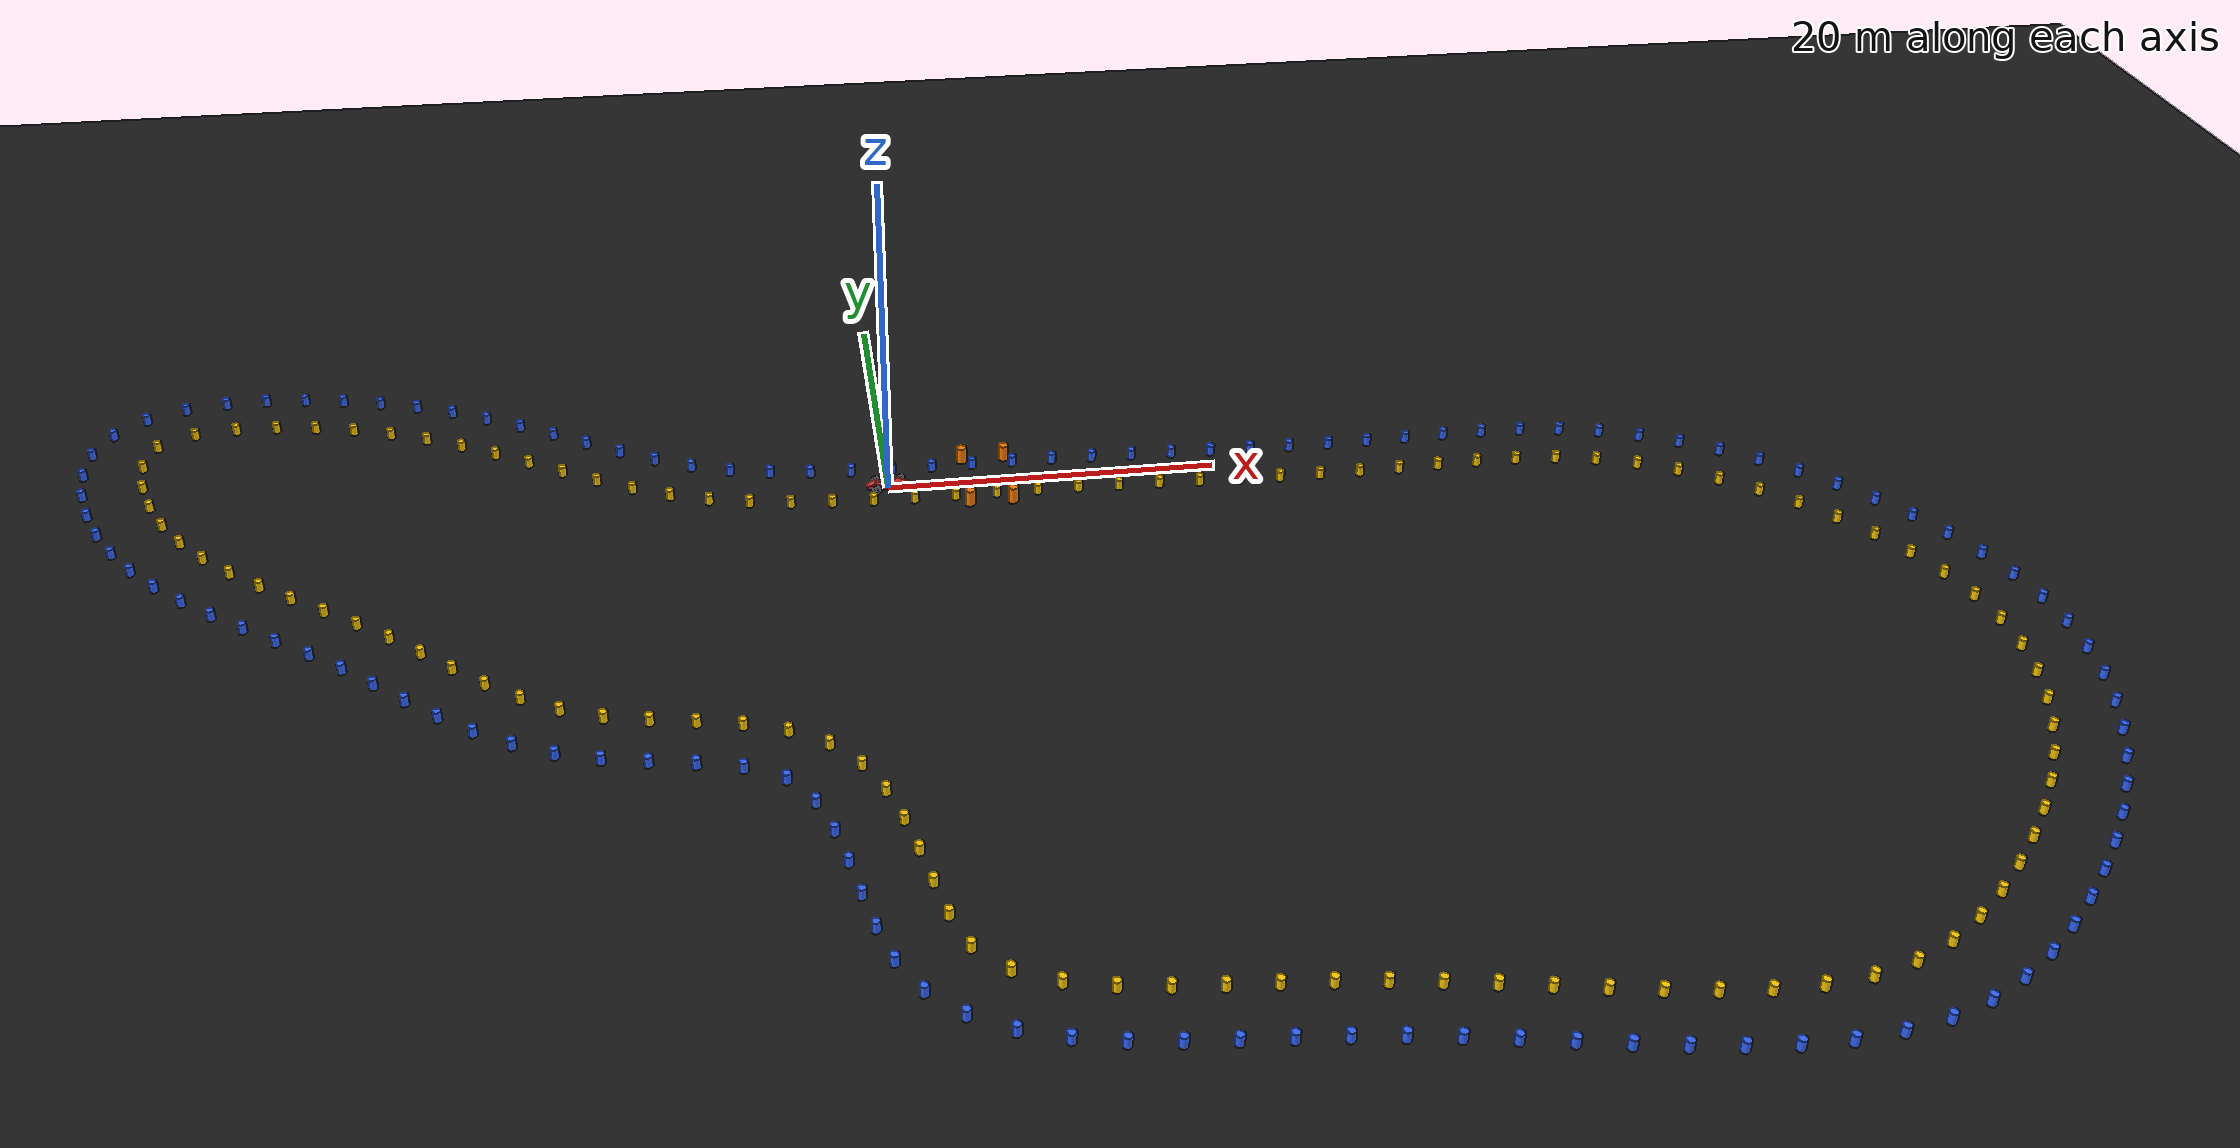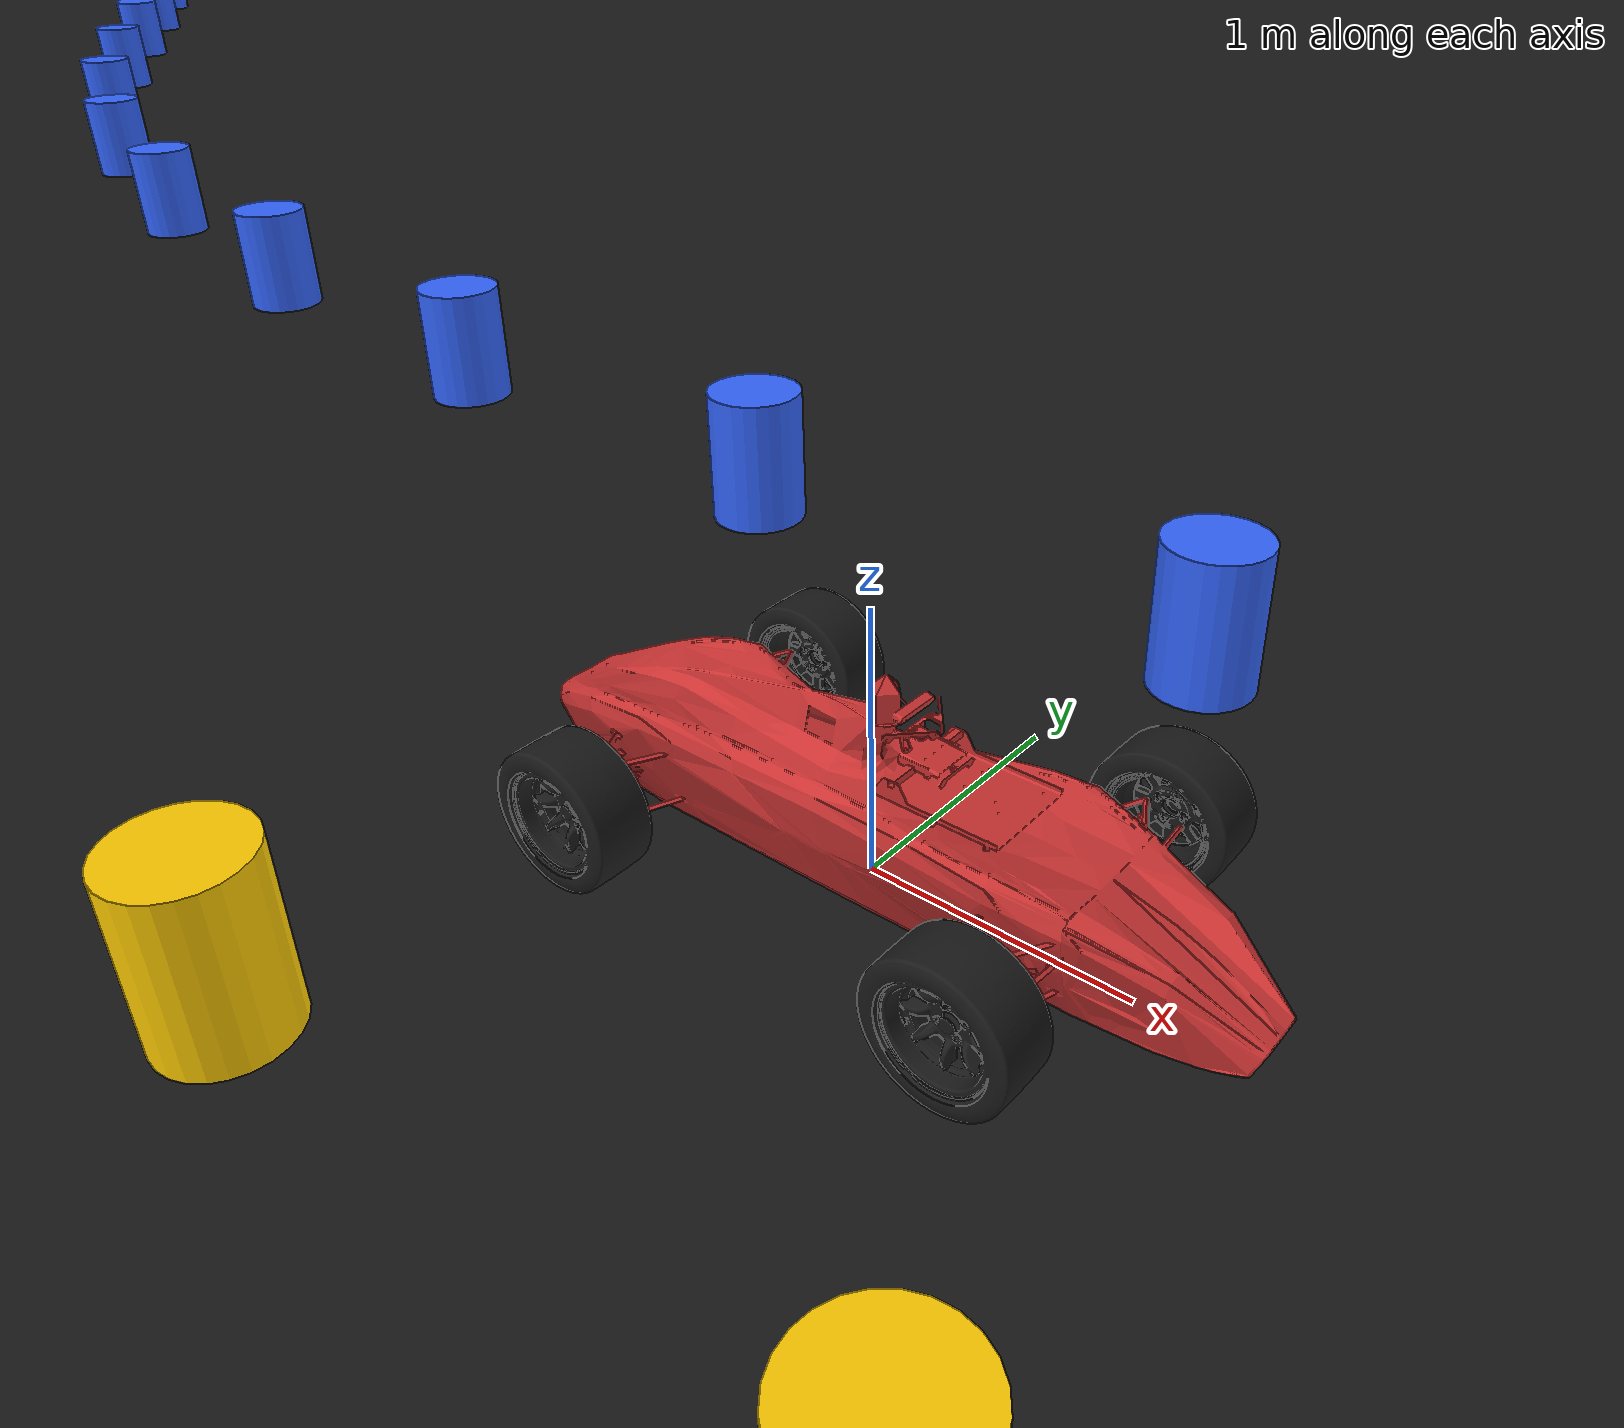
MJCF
<mujoco model="track_scene">
    <compiler angle="radian"/>
    <size njmax="500" nconmax="100"/>
    <option timestep="0.01"/>

    <include file="track_5/track.xml"/>
    <include file="formula_student/base_car/ads_dv.xml"/>

    <visual>
        <headlight ambient="0.6 0.6 0.6" diffuse="0.8 0.8 0.8" specular="0.2 0.2 0.2"/>
        <map znear="0.001"/>
    </visual>

    <asset>
        <texture name="skybox" type="skybox" builtin="gradient" rgb1="0.3 0.5 0.7" rgb2="0 0 0" width="512" height="512"/>

        <!-- Ground texture -->
        <texture name="texplane" type="2d" builtin="checker"
                 rgb1="0.2 0.3 0.4" rgb2="0.3 0.4 0.5"
                 width="512" height="512" mark="none"/>

        <!-- Ground material -->
        <material name="matplane"
                  texture="texplane"
                  texrepeat="10 10"
                  reflectance="0.0"/>
    </asset>

    <worldbody>
        <geom name="floor" type="plane" size="-1 -1 0.1" rgba="0.1 0.1 0.1 1.0" condim="3" friction="1.0 0.005 0.0001" material="matplane"/>
    </worldbody>

</mujoco>

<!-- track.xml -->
<mujoco model="random_track">
  <compiler angle="radian" coordinate="local" autolimits="true"/>
  <default>
    <default class="cone">
      <joint type="free" damping="0.1" frictionloss="0.05"/>
      <geom condim="4" friction="0.5 0.005 0.0001" solref="0.02 1.0" solimp="0.99 0.99 0.001"/>
    </default>
  </default>
  <asset>
    <material name="blue_cone" rgba="0.2 0.4 1.0 1.0" specular="0.5" shininess="0.2"/>
    <material name="yellow_cone" rgba="1.0 0.8 0.0 1.0" specular="0.5" shininess="0.2"/>
    <material name="orange_cone" rgba="1.0 0.5 0.0 1.0" specular="0.5" shininess="0.2"/>
  </asset>
  <worldbody>
    <body name="cone_left_0000" pos="-30.906180928299104 -15.274247821855631 0.325">
      <joint name="cone_left_joint_0000" type="free" damping="0.1" frictionloss="0.05"/>
      <geom name="cone_left_vis_0000" type="cylinder" size="0.228 0.325" material="blue_cone" mass="1.0" density="100" condim="4" friction="0.5 0.005 0.0001" solref="0.02 1.0" solimp="0.99 0.99 0.001"/>
    </body>
    <body name="cone_left_0001" pos="-32.81239513285843 -13.688852993316502 0.325">
      <joint name="cone_left_joint_0001" type="free" damping="0.1" frictionloss="0.05"/>
      <geom name="cone_left_vis_0001" type="cylinder" size="0.228 0.325" material="blue_cone" mass="1.0" density="100" condim="4" friction="0.5 0.005 0.0001" solref="0.02 1.0" solimp="0.99 0.99 0.001"/>
    </body>
    <body name="cone_left_0002" pos="-34.77166783472848 -12.169217330912524 0.325">
      <joint name="cone_left_joint_0002" type="free" damping="0.1" frictionloss="0.05"/>
      <geom name="cone_left_vis_0002" type="cylinder" size="0.228 0.325" material="blue_cone" mass="1.0" density="100" condim="4" friction="0.5 0.005 0.0001" solref="0.02 1.0" solimp="0.99 0.99 0.001"/>
    </body>
    <body name="cone_left_0003" pos="-36.743242516570504 -10.665503903198886 0.325">
      <joint name="cone_left_joint_0003" type="free" damping="0.1" frictionloss="0.05"/>
      <geom name="cone_left_vis_0003" type="cylinder" size="0.228 0.325" material="blue_cone" mass="1.0" density="100" condim="4" friction="0.5 0.005 0.0001" solref="0.02 1.0" solimp="0.99 0.99 0.001"/>
    </body>
    <body name="cone_left_0004" pos="-38.68873652653192 -9.128340026026219 0.325">
      <joint name="cone_left_joint_0004" type="free" damping="0.1" frictionloss="0.05"/>
      <geom name="cone_left_vis_0004" type="cylinder" size="0.228 0.325" material="blue_cone" mass="1.0" density="100" condim="4" friction="0.5 0.005 0.0001" solref="0.02 1.0" solimp="0.99 0.99 0.001"/>
    </body>
    <body name="cone_left_0005" pos="-40.569152057739686 -7.51251910827499 0.325">
      <joint name="cone_left_joint_0005" type="free" damping="0.1" frictionloss="0.05"/>
      <geom name="cone_left_vis_0005" type="cylinder" size="0.228 0.325" material="blue_cone" mass="1.0" density="100" condim="4" friction="0.5 0.005 0.0001" solref="0.02 1.0" solimp="0.99 0.99 0.001"/>
    </body>
    <body name="cone_left_0006" pos="-42.342583557906 -5.7803570120508745 0.325">
      <joint name="cone_left_joint_0006" type="free" damping="0.1" frictionloss="0.05"/>
      <geom name="cone_left_vis_0006" type="cylinder" size="0.228 0.325" material="blue_cone" mass="1.0" density="100" condim="4" friction="0.5 0.005 0.0001" solref="0.02 1.0" solimp="0.99 0.99 0.001"/>
    </body>
    <body name="cone_left_0007" pos="-43.966852289971804 -3.9079906613202553 0.325">
      <joint name="cone_left_joint_0007" type="free" damping="0.1" frictionloss="0.05"/>
      <geom name="cone_left_vis_0007" type="cylinder" size="0.228 0.325" material="blue_cone" mass="1.0" density="100" condim="4" friction="0.5 0.005 0.0001" solref="0.02 1.0" solimp="0.99 0.99 0.001"/>
    </body>
    <body name="cone_left_0008" pos="-45.40187703410106 -1.887175200676607 0.325">
      <joint name="cone_left_joint_0008" type="free" damping="0.1" frictionloss="0.05"/>
      <geom name="cone_left_vis_0008" type="cylinder" size="0.228 0.325" material="blue_cone" mass="1.0" density="100" condim="4" friction="0.5 0.005 0.0001" solref="0.02 1.0" solimp="0.99 0.99 0.001"/>
    </body>
    <body name="cone_left_0009" pos="-46.61776860134746 0.27247802421969425 0.325">
      <joint name="cone_left_joint_0009" type="free" damping="0.1" frictionloss="0.05"/>
      <geom name="cone_left_vis_0009" type="cylinder" size="0.228 0.325" material="blue_cone" mass="1.0" density="100" condim="4" friction="0.5 0.005 0.0001" solref="0.02 1.0" solimp="0.99 0.99 0.001"/>
    </body>
    <body name="cone_left_0010" pos="-47.60061061160969 2.5477022200077 0.325">
      <joint name="cone_left_joint_0010" type="free" damping="0.1" frictionloss="0.05"/>
      <geom name="cone_left_vis_0010" type="cylinder" size="0.228 0.325" material="blue_cone" mass="1.0" density="100" condim="4" friction="0.5 0.005 0.0001" solref="0.02 1.0" solimp="0.99 0.99 0.001"/>
    </body>
    <body name="cone_left_0011" pos="-48.32690365013784 4.916985390767823 0.325">
      <joint name="cone_left_joint_0011" type="free" damping="0.1" frictionloss="0.05"/>
      <geom name="cone_left_vis_0011" type="cylinder" size="0.228 0.325" material="blue_cone" mass="1.0" density="100" condim="4" friction="0.5 0.005 0.0001" solref="0.02 1.0" solimp="0.99 0.99 0.001"/>
    </body>
    <body name="cone_left_0012" pos="-48.722371737893745 7.362052594190686 0.325">
      <joint name="cone_left_joint_0012" type="free" damping="0.1" frictionloss="0.05"/>
      <geom name="cone_left_vis_0012" type="cylinder" size="0.228 0.325" material="blue_cone" mass="1.0" density="100" condim="4" friction="0.5 0.005 0.0001" solref="0.02 1.0" solimp="0.99 0.99 0.001"/>
    </body>
    <body name="cone_left_0013" pos="-48.618158779395046 9.832738219717099 0.325">
      <joint name="cone_left_joint_0013" type="free" damping="0.1" frictionloss="0.05"/>
      <geom name="cone_left_vis_0013" type="cylinder" size="0.228 0.325" material="blue_cone" mass="1.0" density="100" condim="4" friction="0.5 0.005 0.0001" solref="0.02 1.0" solimp="0.99 0.99 0.001"/>
    </body>
    <body name="cone_left_0014" pos="-47.74205530894124 12.13490246340396 0.325">
      <joint name="cone_left_joint_0014" type="free" damping="0.1" frictionloss="0.05"/>
      <geom name="cone_left_vis_0014" type="cylinder" size="0.228 0.325" material="blue_cone" mass="1.0" density="100" condim="4" friction="0.5 0.005 0.0001" solref="0.02 1.0" solimp="0.99 0.99 0.001"/>
    </body>
    <body name="cone_left_0015" pos="-45.99569816213563 13.869484864075355 0.325">
      <joint name="cone_left_joint_0015" type="free" damping="0.1" frictionloss="0.05"/>
      <geom name="cone_left_vis_0015" type="cylinder" size="0.228 0.325" material="blue_cone" mass="1.0" density="100" condim="4" friction="0.5 0.005 0.0001" solref="0.02 1.0" solimp="0.99 0.99 0.001"/>
    </body>
    <body name="cone_left_0016" pos="-43.73932124684589 14.874593527737108 0.325">
      <joint name="cone_left_joint_0016" type="free" damping="0.1" frictionloss="0.05"/>
      <geom name="cone_left_vis_0016" type="cylinder" size="0.228 0.325" material="blue_cone" mass="1.0" density="100" condim="4" friction="0.5 0.005 0.0001" solref="0.02 1.0" solimp="0.99 0.99 0.001"/>
    </body>
    <body name="cone_left_0017" pos="-41.302023929831556 15.308917002851963 0.325">
      <joint name="cone_left_joint_0017" type="free" damping="0.1" frictionloss="0.05"/>
      <geom name="cone_left_vis_0017" type="cylinder" size="0.228 0.325" material="blue_cone" mass="1.0" density="100" condim="4" friction="0.5 0.005 0.0001" solref="0.02 1.0" solimp="0.99 0.99 0.001"/>
    </body>
    <body name="cone_left_0018" pos="-38.82464448697732 15.35670054241953 0.325">
      <joint name="cone_left_joint_0018" type="free" damping="0.1" frictionloss="0.05"/>
      <geom name="cone_left_vis_0018" type="cylinder" size="0.228 0.325" material="blue_cone" mass="1.0" density="100" condim="4" friction="0.5 0.005 0.0001" solref="0.02 1.0" solimp="0.99 0.99 0.001"/>
    </body>
    <body name="cone_left_0019" pos="-36.356132073126886 15.133133623747291 0.325">
      <joint name="cone_left_joint_0019" type="free" damping="0.1" frictionloss="0.05"/>
      <geom name="cone_left_vis_0019" type="cylinder" size="0.228 0.325" material="blue_cone" mass="1.0" density="100" condim="4" friction="0.5 0.005 0.0001" solref="0.02 1.0" solimp="0.99 0.99 0.001"/>
    </body>
    <body name="cone_left_0020" pos="-33.91541829856426 14.699606270096766 0.325">
      <joint name="cone_left_joint_0020" type="free" damping="0.1" frictionloss="0.05"/>
      <geom name="cone_left_vis_0020" type="cylinder" size="0.228 0.325" material="blue_cone" mass="1.0" density="100" condim="4" friction="0.5 0.005 0.0001" solref="0.02 1.0" solimp="0.99 0.99 0.001"/>
    </body>
    <body name="cone_left_0021" pos="-31.513845920144668 14.084861004716567 0.325">
      <joint name="cone_left_joint_0021" type="free" damping="0.1" frictionloss="0.05"/>
      <geom name="cone_left_vis_0021" type="cylinder" size="0.228 0.325" material="blue_cone" mass="1.0" density="100" condim="4" friction="0.5 0.005 0.0001" solref="0.02 1.0" solimp="0.99 0.99 0.001"/>
    </body>
    <body name="cone_left_0022" pos="-29.163930025072162 13.295382594672853 0.325">
      <joint name="cone_left_joint_0022" type="free" damping="0.1" frictionloss="0.05"/>
      <geom name="cone_left_vis_0022" type="cylinder" size="0.228 0.325" material="blue_cone" mass="1.0" density="100" condim="4" friction="0.5 0.005 0.0001" solref="0.02 1.0" solimp="0.99 0.99 0.001"/>
    </body>
    <body name="cone_left_0023" pos="-26.87739480766369 12.337548149697783 0.325">
      <joint name="cone_left_joint_0023" type="free" damping="0.1" frictionloss="0.05"/>
      <geom name="cone_left_vis_0023" type="cylinder" size="0.228 0.325" material="blue_cone" mass="1.0" density="100" condim="4" friction="0.5 0.005 0.0001" solref="0.02 1.0" solimp="0.99 0.99 0.001"/>
    </body>
    <body name="cone_left_0024" pos="-24.65914709782794 11.230455320014709 0.325">
      <joint name="cone_left_joint_0024" type="free" damping="0.1" frictionloss="0.05"/>
      <geom name="cone_left_vis_0024" type="cylinder" size="0.228 0.325" material="blue_cone" mass="1.0" density="100" condim="4" friction="0.5 0.005 0.0001" solref="0.02 1.0" solimp="0.99 0.99 0.001"/>
    </body>
    <body name="cone_left_0025" pos="-22.50535960196105 10.00234552574535 0.325">
      <joint name="cone_left_joint_0025" type="free" damping="0.1" frictionloss="0.05"/>
      <geom name="cone_left_vis_0025" type="cylinder" size="0.228 0.325" material="blue_cone" mass="1.0" density="100" condim="4" friction="0.5 0.005 0.0001" solref="0.02 1.0" solimp="0.99 0.99 0.001"/>
    </body>
    <body name="cone_left_0026" pos="-20.401703059942015 8.68993107601801 0.325">
      <joint name="cone_left_joint_0026" type="free" damping="0.1" frictionloss="0.05"/>
      <geom name="cone_left_vis_0026" type="cylinder" size="0.228 0.325" material="blue_cone" mass="1.0" density="100" condim="4" friction="0.5 0.005 0.0001" solref="0.02 1.0" solimp="0.99 0.99 0.001"/>
    </body>
    <body name="cone_left_0027" pos="-18.32283012461554 7.338436939098921 0.325">
      <joint name="cone_left_joint_0027" type="free" damping="0.1" frictionloss="0.05"/>
      <geom name="cone_left_vis_0027" type="cylinder" size="0.228 0.325" material="blue_cone" mass="1.0" density="100" condim="4" friction="0.5 0.005 0.0001" solref="0.02 1.0" solimp="0.99 0.99 0.001"/>
    </body>
    <body name="cone_left_0028" pos="-16.233745326022945 6.0028746106671065 0.325">
      <joint name="cone_left_joint_0028" type="free" damping="0.1" frictionloss="0.05"/>
      <geom name="cone_left_vis_0028" type="cylinder" size="0.228 0.325" material="blue_cone" mass="1.0" density="100" condim="4" friction="0.5 0.005 0.0001" solref="0.02 1.0" solimp="0.99 0.99 0.001"/>
    </body>
    <body name="cone_left_0029" pos="-14.093236811430785 4.751976648656619 0.325">
      <joint name="cone_left_joint_0029" type="free" damping="0.1" frictionloss="0.05"/>
      <geom name="cone_left_vis_0029" type="cylinder" size="0.228 0.325" material="blue_cone" mass="1.0" density="100" condim="4" friction="0.5 0.005 0.0001" solref="0.02 1.0" solimp="0.99 0.99 0.001"/>
    </body>
    <body name="cone_left_0030" pos="-11.862712671720509 3.6711924400086158 0.325">
      <joint name="cone_left_joint_0030" type="free" damping="0.1" frictionloss="0.05"/>
      <geom name="cone_left_vis_0030" type="cylinder" size="0.228 0.325" material="blue_cone" mass="1.0" density="100" condim="4" friction="0.5 0.005 0.0001" solref="0.02 1.0" solimp="0.99 0.99 0.001"/>
    </body>
    <body name="cone_left_0031" pos="-9.523649561273658 2.8535924845959375 0.325">
      <joint name="cone_left_joint_0031" type="free" damping="0.1" frictionloss="0.05"/>
      <geom name="cone_left_vis_0031" type="cylinder" size="0.228 0.325" material="blue_cone" mass="1.0" density="100" condim="4" friction="0.5 0.005 0.0001" solref="0.02 1.0" solimp="0.99 0.99 0.001"/>
    </body>
    <body name="cone_left_0032" pos="-7.10411323190506 2.316262563103866 0.325">
      <joint name="cone_left_joint_0032" type="free" damping="0.1" frictionloss="0.05"/>
      <geom name="cone_left_vis_0032" type="cylinder" size="0.228 0.325" material="blue_cone" mass="1.0" density="100" condim="4" friction="0.5 0.005 0.0001" solref="0.02 1.0" solimp="0.99 0.99 0.001"/>
    </body>
    <body name="cone_left_0033" pos="-4.646470686657082 1.9914425525255783 0.325">
      <joint name="cone_left_joint_0033" type="free" damping="0.1" frictionloss="0.05"/>
      <geom name="cone_left_vis_0033" type="cylinder" size="0.228 0.325" material="blue_cone" mass="1.0" density="100" condim="4" friction="0.5 0.005 0.0001" solref="0.02 1.0" solimp="0.99 0.99 0.001"/>
    </body>
    <body name="cone_left_0034" pos="-2.1732556281815008 1.8177124783340428 0.325">
      <joint name="cone_left_joint_0034" type="free" damping="0.1" frictionloss="0.05"/>
      <geom name="cone_left_vis_0034" type="cylinder" size="0.228 0.325" material="blue_cone" mass="1.0" density="100" condim="4" friction="0.5 0.005 0.0001" solref="0.02 1.0" solimp="0.99 0.99 0.001"/>
    </body>
    <body name="cone_left_0035" pos="0.30515488735135676 1.7453824299294673 0.325">
      <joint name="cone_left_joint_0035" type="free" damping="0.1" frictionloss="0.05"/>
      <geom name="cone_left_vis_0035" type="cylinder" size="0.228 0.325" material="blue_cone" mass="1.0" density="100" condim="4" friction="0.5 0.005 0.0001" solref="0.02 1.0" solimp="0.99 0.99 0.001"/>
    </body>
    <body name="cone_left_0036" pos="2.7846688142644425 1.7334836540228178 0.325">
      <joint name="cone_left_joint_0036" type="free" damping="0.1" frictionloss="0.05"/>
      <geom name="cone_left_vis_0036" type="cylinder" size="0.228 0.325" material="blue_cone" mass="1.0" density="100" condim="4" friction="0.5 0.005 0.0001" solref="0.02 1.0" solimp="0.99 0.99 0.001"/>
    </body>
    <body name="cone_left_0037" pos="5.264206364933244 1.7463231833725992 0.325">
      <joint name="cone_left_joint_0037" type="free" damping="0.1" frictionloss="0.05"/>
      <geom name="cone_left_vis_0037" type="cylinder" size="0.228 0.325" material="blue_cone" mass="1.0" density="100" condim="4" friction="0.5 0.005 0.0001" solref="0.02 1.0" solimp="0.99 0.99 0.001"/>
    </body>
    <body name="cone_left_0038" pos="7.743763901843451 1.7507712724795343 0.325">
      <joint name="cone_left_joint_0038" type="free" damping="0.1" frictionloss="0.05"/>
      <geom name="cone_left_vis_0038" type="cylinder" size="0.228 0.325" material="blue_cone" mass="1.0" density="100" condim="4" friction="0.5 0.005 0.0001" solref="0.02 1.0" solimp="0.99 0.99 0.001"/>
    </body>
    <body name="cone_left_0039" pos="10.223170539168954 1.7236596486142872 0.325">
      <joint name="cone_left_joint_0039" type="free" damping="0.1" frictionloss="0.05"/>
      <geom name="cone_left_vis_0039" type="cylinder" size="0.228 0.325" material="blue_cone" mass="1.0" density="100" condim="4" friction="0.5 0.005 0.0001" solref="0.02 1.0" solimp="0.99 0.99 0.001"/>
    </body>
    <body name="cone_left_0040" pos="12.702123485612084 1.6686759848274448 0.325">
      <joint name="cone_left_joint_0040" type="free" damping="0.1" frictionloss="0.05"/>
      <geom name="cone_left_vis_0040" type="cylinder" size="0.228 0.325" material="blue_cone" mass="1.0" density="100" condim="4" friction="0.5 0.005 0.0001" solref="0.02 1.0" solimp="0.99 0.99 0.001"/>
    </body>
    <body name="cone_left_0041" pos="15.180585777525444 1.5946155206596213 0.325">
      <joint name="cone_left_joint_0041" type="free" damping="0.1" frictionloss="0.05"/>
      <geom name="cone_left_vis_0041" type="cylinder" size="0.228 0.325" material="blue_cone" mass="1.0" density="100" condim="4" friction="0.5 0.005 0.0001" solref="0.02 1.0" solimp="0.99 0.99 0.001"/>
    </body>
    <body name="cone_left_0042" pos="17.65874429705974 1.510910037943713 0.325">
      <joint name="cone_left_joint_0042" type="free" damping="0.1" frictionloss="0.05"/>
      <geom name="cone_left_vis_0042" type="cylinder" size="0.228 0.325" material="blue_cone" mass="1.0" density="100" condim="4" friction="0.5 0.005 0.0001" solref="0.02 1.0" solimp="0.99 0.99 0.001"/>
    </body>
    <body name="cone_left_0043" pos="20.136913550939184 1.4275266344439217 0.325">
      <joint name="cone_left_joint_0043" type="free" damping="0.1" frictionloss="0.05"/>
      <geom name="cone_left_vis_0043" type="cylinder" size="0.228 0.325" material="blue_cone" mass="1.0" density="100" condim="4" friction="0.5 0.005 0.0001" solref="0.02 1.0" solimp="0.99 0.99 0.001"/>
    </body>
    <body name="cone_left_0044" pos="22.615414728518303 1.3548044840307956 0.325">
      <joint name="cone_left_joint_0044" type="free" damping="0.1" frictionloss="0.05"/>
      <geom name="cone_left_vis_0044" type="cylinder" size="0.228 0.325" material="blue_cone" mass="1.0" density="100" condim="4" friction="0.5 0.005 0.0001" solref="0.02 1.0" solimp="0.99 0.99 0.001"/>
    </body>
    <body name="cone_left_0045" pos="25.0944394329221 1.3032743527408748 0.325">
      <joint name="cone_left_joint_0045" type="free" damping="0.1" frictionloss="0.05"/>
      <geom name="cone_left_vis_0045" type="cylinder" size="0.228 0.325" material="blue_cone" mass="1.0" density="100" condim="4" friction="0.5 0.005 0.0001" solref="0.02 1.0" solimp="0.99 0.99 0.001"/>
    </body>
    <body name="cone_left_0046" pos="27.573909444448148 1.2834558041592974 0.325">
      <joint name="cone_left_joint_0046" type="free" damping="0.1" frictionloss="0.05"/>
      <geom name="cone_left_vis_0046" type="cylinder" size="0.228 0.325" material="blue_cone" mass="1.0" density="100" condim="4" friction="0.5 0.005 0.0001" solref="0.02 1.0" solimp="0.99 0.99 0.001"/>
    </body>
    <body name="cone_left_0047" pos="30.05334471215386 1.3056984431182883 0.325">
      <joint name="cone_left_joint_0047" type="free" damping="0.1" frictionloss="0.05"/>
      <geom name="cone_left_vis_0047" type="cylinder" size="0.228 0.325" material="blue_cone" mass="1.0" density="100" condim="4" friction="0.5 0.005 0.0001" solref="0.02 1.0" solimp="0.99 0.99 0.001"/>
    </body>
    <body name="cone_left_0048" pos="32.53179873891719 1.3786523388563232 0.325">
      <joint name="cone_left_joint_0048" type="free" damping="0.1" frictionloss="0.05"/>
      <geom name="cone_left_vis_0048" type="cylinder" size="0.228 0.325" material="blue_cone" mass="1.0" density="100" condim="4" friction="0.5 0.005 0.0001" solref="0.02 1.0" solimp="0.99 0.99 0.001"/>
    </body>
    <body name="cone_left_0049" pos="35.0096219723943 1.471573898938761 0.325">
      <joint name="cone_left_joint_0049" type="free" damping="0.1" frictionloss="0.05"/>
      <geom name="cone_left_vis_0049" type="cylinder" size="0.228 0.325" material="blue_cone" mass="1.0" density="100" condim="4" friction="0.5 0.005 0.0001" solref="0.02 1.0" solimp="0.99 0.99 0.001"/>
    </body>
    <body name="cone_left_0050" pos="37.48877778862669 1.5075240445214622 0.325">
      <joint name="cone_left_joint_0050" type="free" damping="0.1" frictionloss="0.05"/>
      <geom name="cone_left_vis_0050" type="cylinder" size="0.228 0.325" material="blue_cone" mass="1.0" density="100" condim="4" friction="0.5 0.005 0.0001" solref="0.02 1.0" solimp="0.99 0.99 0.001"/>
    </body>
    <body name="cone_left_0051" pos="39.96596007041143 1.4105974181701288 0.325">
      <joint name="cone_left_joint_0051" type="free" damping="0.1" frictionloss="0.05"/>
      <geom name="cone_left_vis_0051" type="cylinder" size="0.228 0.325" material="blue_cone" mass="1.0" density="100" condim="4" friction="0.5 0.005 0.0001" solref="0.02 1.0" solimp="0.99 0.99 0.001"/>
    </body>
    <body name="cone_left_0052" pos="42.42621859777128 1.1096887019168005 0.325">
      <joint name="cone_left_joint_0052" type="free" damping="0.1" frictionloss="0.05"/>
      <geom name="cone_left_vis_0052" type="cylinder" size="0.228 0.325" material="blue_cone" mass="1.0" density="100" condim="4" friction="0.5 0.005 0.0001" solref="0.02 1.0" solimp="0.99 0.99 0.001"/>
    </body>
    <body name="cone_left_0053" pos="44.83928206074407 0.5455149705192852 0.325">
      <joint name="cone_left_joint_0053" type="free" damping="0.1" frictionloss="0.05"/>
      <geom name="cone_left_vis_0053" type="cylinder" size="0.228 0.325" material="blue_cone" mass="1.0" density="100" condim="4" friction="0.5 0.005 0.0001" solref="0.02 1.0" solimp="0.99 0.99 0.001"/>
    </body>
    <body name="cone_left_0054" pos="47.17235360154801 -0.2905084410636469 0.325">
      <joint name="cone_left_joint_0054" type="free" damping="0.1" frictionloss="0.05"/>
      <geom name="cone_left_vis_0054" type="cylinder" size="0.228 0.325" material="blue_cone" mass="1.0" density="100" condim="4" friction="0.5 0.005 0.0001" solref="0.02 1.0" solimp="0.99 0.99 0.001"/>
    </body>
    <body name="cone_left_0055" pos="49.40551405249418 -1.3657821728992374 0.325">
      <joint name="cone_left_joint_0055" type="free" damping="0.1" frictionloss="0.05"/>
      <geom name="cone_left_vis_0055" type="cylinder" size="0.228 0.325" material="blue_cone" mass="1.0" density="100" condim="4" friction="0.5 0.005 0.0001" solref="0.02 1.0" solimp="0.99 0.99 0.001"/>
    </body>
    <body name="cone_left_0056" pos="51.525421069569205 -2.650274488127442 0.325">
      <joint name="cone_left_joint_0056" type="free" damping="0.1" frictionloss="0.05"/>
      <geom name="cone_left_vis_0056" type="cylinder" size="0.228 0.325" material="blue_cone" mass="1.0" density="100" condim="4" friction="0.5 0.005 0.0001" solref="0.02 1.0" solimp="0.99 0.99 0.001"/>
    </body>
    <body name="cone_left_0057" pos="53.522054098276655 -4.11922494088979 0.325">
      <joint name="cone_left_joint_0057" type="free" damping="0.1" frictionloss="0.05"/>
      <geom name="cone_left_vis_0057" type="cylinder" size="0.228 0.325" material="blue_cone" mass="1.0" density="100" condim="4" friction="0.5 0.005 0.0001" solref="0.02 1.0" solimp="0.99 0.99 0.001"/>
    </body>
    <body name="cone_left_0058" pos="55.38647222797786 -5.752791918087489 0.325">
      <joint name="cone_left_joint_0058" type="free" damping="0.1" frictionloss="0.05"/>
      <geom name="cone_left_vis_0058" type="cylinder" size="0.228 0.325" material="blue_cone" mass="1.0" density="100" condim="4" friction="0.5 0.005 0.0001" solref="0.02 1.0" solimp="0.99 0.99 0.001"/>
    </body>
    <body name="cone_left_0059" pos="57.109138129710246 -7.53523784024992 0.325">
      <joint name="cone_left_joint_0059" type="free" damping="0.1" frictionloss="0.05"/>
      <geom name="cone_left_vis_0059" type="cylinder" size="0.228 0.325" material="blue_cone" mass="1.0" density="100" condim="4" friction="0.5 0.005 0.0001" solref="0.02 1.0" solimp="0.99 0.99 0.001"/>
    </body>
    <body name="cone_left_0060" pos="58.67862262590232 -9.45393119265442 0.325">
      <joint name="cone_left_joint_0060" type="free" damping="0.1" frictionloss="0.05"/>
      <geom name="cone_left_vis_0060" type="cylinder" size="0.228 0.325" material="blue_cone" mass="1.0" density="100" condim="4" friction="0.5 0.005 0.0001" solref="0.02 1.0" solimp="0.99 0.99 0.001"/>
    </body>
    <body name="cone_left_0061" pos="60.080492466633814 -11.498254794501772 0.325">
      <joint name="cone_left_joint_0061" type="free" damping="0.1" frictionloss="0.05"/>
      <geom name="cone_left_vis_0061" type="cylinder" size="0.228 0.325" material="blue_cone" mass="1.0" density="100" condim="4" friction="0.5 0.005 0.0001" solref="0.02 1.0" solimp="0.99 0.99 0.001"/>
    </body>
    <body name="cone_left_0062" pos="61.29622674876953 -13.658363412679876 0.325">
      <joint name="cone_left_joint_0062" type="free" damping="0.1" frictionloss="0.05"/>
      <geom name="cone_left_vis_0062" type="cylinder" size="0.228 0.325" material="blue_cone" mass="1.0" density="100" condim="4" friction="0.5 0.005 0.0001" solref="0.02 1.0" solimp="0.99 0.99 0.001"/>
    </body>
    <body name="cone_left_0063" pos="62.30318245743641 -15.923183554906974 0.325">
      <joint name="cone_left_joint_0063" type="free" damping="0.1" frictionloss="0.05"/>
      <geom name="cone_left_vis_0063" type="cylinder" size="0.228 0.325" material="blue_cone" mass="1.0" density="100" condim="4" friction="0.5 0.005 0.0001" solref="0.02 1.0" solimp="0.99 0.99 0.001"/>
    </body>
    <body name="cone_left_0064" pos="63.073473797283455 -18.278829729356996 0.325">
      <joint name="cone_left_joint_0064" type="free" damping="0.1" frictionloss="0.05"/>
      <geom name="cone_left_vis_0064" type="cylinder" size="0.228 0.325" material="blue_cone" mass="1.0" density="100" condim="4" friction="0.5 0.005 0.0001" solref="0.02 1.0" solimp="0.99 0.99 0.001"/>
    </body>
    <body name="cone_left_0065" pos="63.57447311297169 -20.705802679359287 0.325">
      <joint name="cone_left_joint_0065" type="free" damping="0.1" frictionloss="0.05"/>
      <geom name="cone_left_vis_0065" type="cylinder" size="0.228 0.325" material="blue_cone" mass="1.0" density="100" condim="4" friction="0.5 0.005 0.0001" solref="0.02 1.0" solimp="0.99 0.99 0.001"/>
    </body>
    <body name="cone_left_0066" pos="63.77644637032759 -23.17556828168876 0.325">
      <joint name="cone_left_joint_0066" type="free" damping="0.1" frictionloss="0.05"/>
      <geom name="cone_left_vis_0066" type="cylinder" size="0.228 0.325" material="blue_cone" mass="1.0" density="100" condim="4" friction="0.5 0.005 0.0001" solref="0.02 1.0" solimp="0.99 0.99 0.001"/>
    </body>
    <body name="cone_left_0067" pos="63.681999486008564 -25.651919787936492 0.325">
      <joint name="cone_left_joint_0067" type="free" damping="0.1" frictionloss="0.05"/>
      <geom name="cone_left_vis_0067" type="cylinder" size="0.228 0.325" material="blue_cone" mass="1.0" density="100" condim="4" friction="0.5 0.005 0.0001" solref="0.02 1.0" solimp="0.99 0.99 0.001"/>
    </body>
    <body name="cone_left_0068" pos="63.31219331860841 -28.10253876343458 0.325">
      <joint name="cone_left_joint_0068" type="free" damping="0.1" frictionloss="0.05"/>
      <geom name="cone_left_vis_0068" type="cylinder" size="0.228 0.325" material="blue_cone" mass="1.0" density="100" condim="4" friction="0.5 0.005 0.0001" solref="0.02 1.0" solimp="0.99 0.99 0.001"/>
    </body>
    <body name="cone_left_0069" pos="62.69438741340909 -30.502902160516634 0.325">
      <joint name="cone_left_joint_0069" type="free" damping="0.1" frictionloss="0.05"/>
      <geom name="cone_left_vis_0069" type="cylinder" size="0.228 0.325" material="blue_cone" mass="1.0" density="100" condim="4" friction="0.5 0.005 0.0001" solref="0.02 1.0" solimp="0.99 0.99 0.001"/>
    </body>
    <body name="cone_left_0070" pos="61.8577528868331 -32.83622474279274 0.325">
      <joint name="cone_left_joint_0070" type="free" damping="0.1" frictionloss="0.05"/>
      <geom name="cone_left_vis_0070" type="cylinder" size="0.228 0.325" material="blue_cone" mass="1.0" density="100" condim="4" friction="0.5 0.005 0.0001" solref="0.02 1.0" solimp="0.99 0.99 0.001"/>
    </body>
    <body name="cone_left_0071" pos="60.83110018100203 -35.092557996655145 0.325">
      <joint name="cone_left_joint_0071" type="free" damping="0.1" frictionloss="0.05"/>
      <geom name="cone_left_vis_0071" type="cylinder" size="0.228 0.325" material="blue_cone" mass="1.0" density="100" condim="4" friction="0.5 0.005 0.0001" solref="0.02 1.0" solimp="0.99 0.99 0.001"/>
    </body>
    <body name="cone_left_0072" pos="59.639339201195824 -37.26634500064015 0.325">
      <joint name="cone_left_joint_0072" type="free" damping="0.1" frictionloss="0.05"/>
      <geom name="cone_left_vis_0072" type="cylinder" size="0.228 0.325" material="blue_cone" mass="1.0" density="100" condim="4" friction="0.5 0.005 0.0001" solref="0.02 1.0" solimp="0.99 0.99 0.001"/>
    </body>
    <body name="cone_left_0073" pos="58.30363092062916 -39.35488123752682 0.325">
      <joint name="cone_left_joint_0073" type="free" damping="0.1" frictionloss="0.05"/>
      <geom name="cone_left_vis_0073" type="cylinder" size="0.228 0.325" material="blue_cone" mass="1.0" density="100" condim="4" friction="0.5 0.005 0.0001" solref="0.02 1.0" solimp="0.99 0.99 0.001"/>
    </body>
    <body name="cone_left_0074" pos="56.841401598183296 -41.35696079493872 0.325">
      <joint name="cone_left_joint_0074" type="free" damping="0.1" frictionloss="0.05"/>
      <geom name="cone_left_vis_0074" type="cylinder" size="0.228 0.325" material="blue_cone" mass="1.0" density="100" condim="4" friction="0.5 0.005 0.0001" solref="0.02 1.0" solimp="0.99 0.99 0.001"/>
    </body>
    <body name="cone_left_0075" pos="55.26665871738709 -43.27186627304012 0.325">
      <joint name="cone_left_joint_0075" type="free" damping="0.1" frictionloss="0.05"/>
      <geom name="cone_left_vis_0075" type="cylinder" size="0.228 0.325" material="blue_cone" mass="1.0" density="100" condim="4" friction="0.5 0.005 0.0001" solref="0.02 1.0" solimp="0.99 0.99 0.001"/>
    </body>
    <body name="cone_left_0076" pos="53.590368869054956 -45.09858292356022 0.325">
      <joint name="cone_left_joint_0076" type="free" damping="0.1" frictionloss="0.05"/>
      <geom name="cone_left_vis_0076" type="cylinder" size="0.228 0.325" material="blue_cone" mass="1.0" density="100" condim="4" friction="0.5 0.005 0.0001" solref="0.02 1.0" solimp="0.99 0.99 0.001"/>
    </body>
    <body name="cone_left_0077" pos="51.817264079026174 -46.83139042288975 0.325">
      <joint name="cone_left_joint_0077" type="free" damping="0.1" frictionloss="0.05"/>
      <geom name="cone_left_vis_0077" type="cylinder" size="0.228 0.325" material="blue_cone" mass="1.0" density="100" condim="4" friction="0.5 0.005 0.0001" solref="0.02 1.0" solimp="0.99 0.99 0.001"/>
    </body>
    <body name="cone_left_0078" pos="49.93147311170986 -48.440405731115625 0.325">
      <joint name="cone_left_joint_0078" type="free" damping="0.1" frictionloss="0.05"/>
      <geom name="cone_left_vis_0078" type="cylinder" size="0.228 0.325" material="blue_cone" mass="1.0" density="100" condim="4" friction="0.5 0.005 0.0001" solref="0.02 1.0" solimp="0.99 0.99 0.001"/>
    </body>
    <body name="cone_left_0079" pos="47.909964579939825 -49.87440126925269 0.325">
      <joint name="cone_left_joint_0079" type="free" damping="0.1" frictionloss="0.05"/>
      <geom name="cone_left_vis_0079" type="cylinder" size="0.228 0.325" material="blue_cone" mass="1.0" density="100" condim="4" friction="0.5 0.005 0.0001" solref="0.02 1.0" solimp="0.99 0.99 0.001"/>
    </body>
    <body name="cone_left_0080" pos="45.733581175105726 -51.05854125863817 0.325">
      <joint name="cone_left_joint_0080" type="free" damping="0.1" frictionloss="0.05"/>
      <geom name="cone_left_vis_0080" type="cylinder" size="0.228 0.325" material="blue_cone" mass="1.0" density="100" condim="4" friction="0.5 0.005 0.0001" solref="0.02 1.0" solimp="0.99 0.99 0.001"/>
    </body>
    <body name="cone_left_0081" pos="43.41055214337335 -51.91914426146977 0.325">
      <joint name="cone_left_joint_0081" type="free" damping="0.1" frictionloss="0.05"/>
      <geom name="cone_left_vis_0081" type="cylinder" size="0.228 0.325" material="blue_cone" mass="1.0" density="100" condim="4" friction="0.5 0.005 0.0001" solref="0.02 1.0" solimp="0.99 0.99 0.001"/>
    </body>
    <body name="cone_left_0082" pos="40.98909452209631 -52.44392942463327 0.325">
      <joint name="cone_left_joint_0082" type="free" damping="0.1" frictionloss="0.05"/>
      <geom name="cone_left_vis_0082" type="cylinder" size="0.228 0.325" material="blue_cone" mass="1.0" density="100" condim="4" friction="0.5 0.005 0.0001" solref="0.02 1.0" solimp="0.99 0.99 0.001"/>
    </body>
    <body name="cone_left_0083" pos="38.52064307476353 -52.66373221630818 0.325">
      <joint name="cone_left_joint_0083" type="free" damping="0.1" frictionloss="0.05"/>
      <geom name="cone_left_vis_0083" type="cylinder" size="0.228 0.325" material="blue_cone" mass="1.0" density="100" condim="4" friction="0.5 0.005 0.0001" solref="0.02 1.0" solimp="0.99 0.99 0.001"/>
    </body>
    <body name="cone_left_0084" pos="36.042088684762675 -52.63298135892754 0.325">
      <joint name="cone_left_joint_0084" type="free" damping="0.1" frictionloss="0.05"/>
      <geom name="cone_left_vis_0084" type="cylinder" size="0.228 0.325" material="blue_cone" mass="1.0" density="100" condim="4" friction="0.5 0.005 0.0001" solref="0.02 1.0" solimp="0.99 0.99 0.001"/>
    </body>
    <body name="cone_left_0085" pos="33.57271189005728 -52.413194680567216 0.325">
      <joint name="cone_left_joint_0085" type="free" damping="0.1" frictionloss="0.05"/>
      <geom name="cone_left_vis_0085" type="cylinder" size="0.228 0.325" material="blue_cone" mass="1.0" density="100" condim="4" friction="0.5 0.005 0.0001" solref="0.02 1.0" solimp="0.99 0.99 0.001"/>
    </body>
    <body name="cone_left_0086" pos="31.11833318953113 -52.06196597320468 0.325">
      <joint name="cone_left_joint_0086" type="free" damping="0.1" frictionloss="0.05"/>
      <geom name="cone_left_vis_0086" type="cylinder" size="0.228 0.325" material="blue_cone" mass="1.0" density="100" condim="4" friction="0.5 0.005 0.0001" solref="0.02 1.0" solimp="0.99 0.99 0.001"/>
    </body>
    <body name="cone_left_0087" pos="28.67683967832565 -51.629435018513675 0.325">
      <joint name="cone_left_joint_0087" type="free" damping="0.1" frictionloss="0.05"/>
      <geom name="cone_left_vis_0087" type="cylinder" size="0.228 0.325" material="blue_cone" mass="1.0" density="100" condim="4" friction="0.5 0.005 0.0001" solref="0.02 1.0" solimp="0.99 0.99 0.001"/>
    </body>
    <body name="cone_left_0088" pos="26.242514271347744 -51.15794704904656 0.325">
      <joint name="cone_left_joint_0088" type="free" damping="0.1" frictionloss="0.05"/>
      <geom name="cone_left_vis_0088" type="cylinder" size="0.228 0.325" material="blue_cone" mass="1.0" density="100" condim="4" friction="0.5 0.005 0.0001" solref="0.02 1.0" solimp="0.99 0.99 0.001"/>
    </body>
    <body name="cone_left_0089" pos="23.808740568721817 -50.683598710690696 0.325">
      <joint name="cone_left_joint_0089" type="free" damping="0.1" frictionloss="0.05"/>
      <geom name="cone_left_vis_0089" type="cylinder" size="0.228 0.325" material="blue_cone" mass="1.0" density="100" condim="4" friction="0.5 0.005 0.0001" solref="0.02 1.0" solimp="0.99 0.99 0.001"/>
    </body>
    <body name="cone_left_0090" pos="21.36954163160179 -50.238152491955034 0.325">
      <joint name="cone_left_joint_0090" type="free" damping="0.1" frictionloss="0.05"/>
      <geom name="cone_left_vis_0090" type="cylinder" size="0.228 0.325" material="blue_cone" mass="1.0" density="100" condim="4" friction="0.5 0.005 0.0001" solref="0.02 1.0" solimp="0.99 0.99 0.001"/>
    </body>
    <body name="cone_left_0091" pos="18.92058676482769 -49.85024846620251 0.325">
      <joint name="cone_left_joint_0091" type="free" damping="0.1" frictionloss="0.05"/>
      <geom name="cone_left_vis_0091" type="cylinder" size="0.228 0.325" material="blue_cone" mass="1.0" density="100" condim="4" friction="0.5 0.005 0.0001" solref="0.02 1.0" solimp="0.99 0.99 0.001"/>
    </body>
    <body name="cone_left_0092" pos="16.459899468880167 -49.5460672904591 0.325">
      <joint name="cone_left_joint_0092" type="free" damping="0.1" frictionloss="0.05"/>
      <geom name="cone_left_vis_0092" type="cylinder" size="0.228 0.325" material="blue_cone" mass="1.0" density="100" condim="4" friction="0.5 0.005 0.0001" solref="0.02 1.0" solimp="0.99 0.99 0.001"/>
    </body>
    <body name="cone_left_0093" pos="13.990290092480755 -49.32465359819153 0.325">
      <joint name="cone_left_joint_0093" type="free" damping="0.1" frictionloss="0.05"/>
      <geom name="cone_left_vis_0093" type="cylinder" size="0.228 0.325" material="blue_cone" mass="1.0" density="100" condim="4" friction="0.5 0.005 0.0001" solref="0.02 1.0" solimp="0.99 0.99 0.001"/>
    </body>
    <body name="cone_left_0094" pos="11.518400761632435 -49.12962941815122 0.325">
      <joint name="cone_left_joint_0094" type="free" damping="0.1" frictionloss="0.05"/>
      <geom name="cone_left_vis_0094" type="cylinder" size="0.228 0.325" material="blue_cone" mass="1.0" density="100" condim="4" friction="0.5 0.005 0.0001" solref="0.02 1.0" solimp="0.99 0.99 0.001"/>
    </body>
    <body name="cone_left_0095" pos="9.049571699658635 -48.89989308159944 0.325">
      <joint name="cone_left_joint_0095" type="free" damping="0.1" frictionloss="0.05"/>
      <geom name="cone_left_vis_0095" type="cylinder" size="0.228 0.325" material="blue_cone" mass="1.0" density="100" condim="4" friction="0.5 0.005 0.0001" solref="0.02 1.0" solimp="0.99 0.99 0.001"/>
    </body>
    <body name="cone_left_0096" pos="6.592793743876797 -48.56708019677968 0.325">
      <joint name="cone_left_joint_0096" type="free" damping="0.1" frictionloss="0.05"/>
      <geom name="cone_left_vis_0096" type="cylinder" size="0.228 0.325" material="blue_cone" mass="1.0" density="100" condim="4" friction="0.5 0.005 0.0001" solref="0.02 1.0" solimp="0.99 0.99 0.001"/>
    </body>
    <body name="cone_left_0097" pos="4.169916868437461 -48.04486780249015 0.325">
      <joint name="cone_left_joint_0097" type="free" damping="0.1" frictionloss="0.05"/>
      <geom name="cone_left_vis_0097" type="cylinder" size="0.228 0.325" material="blue_cone" mass="1.0" density="100" condim="4" friction="0.5 0.005 0.0001" solref="0.02 1.0" solimp="0.99 0.99 0.001"/>
    </body>
    <body name="cone_left_0098" pos="1.8347204658878624 -47.2190152360967 0.325">
      <joint name="cone_left_joint_0098" type="free" damping="0.1" frictionloss="0.05"/>
      <geom name="cone_left_vis_0098" type="cylinder" size="0.228 0.325" material="blue_cone" mass="1.0" density="100" condim="4" friction="0.5 0.005 0.0001" solref="0.02 1.0" solimp="0.99 0.99 0.001"/>
    </body>
    <body name="cone_left_0099" pos="-0.29496473537886203 -45.95988361775146 0.325">
      <joint name="cone_left_joint_0099" type="free" damping="0.1" frictionloss="0.05"/>
      <geom name="cone_left_vis_0099" type="cylinder" size="0.228 0.325" material="blue_cone" mass="1.0" density="100" condim="4" friction="0.5 0.005 0.0001" solref="0.02 1.0" solimp="0.99 0.99 0.001"/>
    </body>
    <body name="cone_left_0100" pos="-2.0244499908134728 -44.194858232721224 0.325">
      <joint name="cone_left_joint_0100" type="free" damping="0.1" frictionloss="0.05"/>
      <geom name="cone_left_vis_0100" type="cylinder" size="0.228 0.325" material="blue_cone" mass="1.0" density="100" condim="4" friction="0.5 0.005 0.0001" solref="0.02 1.0" solimp="0.99 0.99 0.001"/>
    </body>
    <body name="cone_left_0101" pos="-3.177838846210591 -42.00902741140917 0.325">
      <joint name="cone_left_joint_0101" type="free" damping="0.1" frictionloss="0.05"/>
      <geom name="cone_left_vis_0101" type="cylinder" size="0.228 0.325" material="blue_cone" mass="1.0" density="100" condim="4" friction="0.5 0.005 0.0001" solref="0.02 1.0" solimp="0.99 0.99 0.001"/>
    </body>
    <body name="cone_left_0102" pos="-3.850238315448692 -39.62418167953147 0.325">
      <joint name="cone_left_joint_0102" type="free" damping="0.1" frictionloss="0.05"/>
      <geom name="cone_left_vis_0102" type="cylinder" size="0.228 0.325" material="blue_cone" mass="1.0" density="100" condim="4" friction="0.5 0.005 0.0001" solref="0.02 1.0" solimp="0.99 0.99 0.001"/>
    </body>
    <body name="cone_left_0103" pos="-4.3405233424279785 -37.193730883587904 0.325">
      <joint name="cone_left_joint_0103" type="free" damping="0.1" frictionloss="0.05"/>
      <geom name="cone_left_vis_0103" type="cylinder" size="0.228 0.325" material="blue_cone" mass="1.0" density="100" condim="4" friction="0.5 0.005 0.0001" solref="0.02 1.0" solimp="0.99 0.99 0.001"/>
    </body>
    <body name="cone_left_0104" pos="-4.793326045858464 -34.755864349726174 0.325">
      <joint name="cone_left_joint_0104" type="free" damping="0.1" frictionloss="0.05"/>
      <geom name="cone_left_vis_0104" type="cylinder" size="0.228 0.325" material="blue_cone" mass="1.0" density="100" condim="4" friction="0.5 0.005 0.0001" solref="0.02 1.0" solimp="0.99 0.99 0.001"/>
    </body>
    <body name="cone_left_0105" pos="-5.329089062650901 -32.335290886964955 0.325">
      <joint name="cone_left_joint_0105" type="free" damping="0.1" frictionloss="0.05"/>
      <geom name="cone_left_vis_0105" type="cylinder" size="0.228 0.325" material="blue_cone" mass="1.0" density="100" condim="4" friction="0.5 0.005 0.0001" solref="0.02 1.0" solimp="0.99 0.99 0.001"/>
    </body>
    <body name="cone_left_0106" pos="-6.116635087419382 -29.98685844426756 0.325">
      <joint name="cone_left_joint_0106" type="free" damping="0.1" frictionloss="0.05"/>
      <geom name="cone_left_vis_0106" type="cylinder" size="0.228 0.325" material="blue_cone" mass="1.0" density="100" condim="4" friction="0.5 0.005 0.0001" solref="0.02 1.0" solimp="0.99 0.99 0.001"/>
    </body>
    <body name="cone_left_0107" pos="-7.469897881355948 -27.927966375502542 0.325">
      <joint name="cone_left_joint_0107" type="free" damping="0.1" frictionloss="0.05"/>
      <geom name="cone_left_vis_0107" type="cylinder" size="0.228 0.325" material="blue_cone" mass="1.0" density="100" condim="4" friction="0.5 0.005 0.0001" solref="0.02 1.0" solimp="0.99 0.99 0.001"/>
    </body>
    <body name="cone_left_0108" pos="-9.610514193456886 -26.71568774989084 0.325">
      <joint name="cone_left_joint_0108" type="free" damping="0.1" frictionloss="0.05"/>
      <geom name="cone_left_vis_0108" type="cylinder" size="0.228 0.325" material="blue_cone" mass="1.0" density="100" condim="4" friction="0.5 0.005 0.0001" solref="0.02 1.0" solimp="0.99 0.99 0.001"/>
    </body>
    <body name="cone_left_0109" pos="-12.007627372138224 -26.08884122096952 0.325">
      <joint name="cone_left_joint_0109" type="free" damping="0.1" frictionloss="0.05"/>
      <geom name="cone_left_vis_0109" type="cylinder" size="0.228 0.325" material="blue_cone" mass="1.0" density="100" condim="4" friction="0.5 0.005 0.0001" solref="0.02 1.0" solimp="0.99 0.99 0.001"/>
    </body>
    <body name="cone_left_0110" pos="-14.443583077620296 -25.625994253845192 0.325">
      <joint name="cone_left_joint_0110" type="free" damping="0.1" frictionloss="0.05"/>
      <geom name="cone_left_vis_0110" type="cylinder" size="0.228 0.325" material="blue_cone" mass="1.0" density="100" condim="4" friction="0.5 0.005 0.0001" solref="0.02 1.0" solimp="0.99 0.99 0.001"/>
    </body>
    <body name="cone_left_0111" pos="-16.866831977076885 -25.10251935536568 0.325">
      <joint name="cone_left_joint_0111" type="free" damping="0.1" frictionloss="0.05"/>
      <geom name="cone_left_vis_0111" type="cylinder" size="0.228 0.325" material="blue_cone" mass="1.0" density="100" condim="4" friction="0.5 0.005 0.0001" solref="0.02 1.0" solimp="0.99 0.99 0.001"/>
    </body>
    <body name="cone_left_0112" pos="-19.22377146186487 -24.338837174495374 0.325">
      <joint name="cone_left_joint_0112" type="free" damping="0.1" frictionloss="0.05"/>
      <geom name="cone_left_vis_0112" type="cylinder" size="0.228 0.325" material="blue_cone" mass="1.0" density="100" condim="4" friction="0.5 0.005 0.0001" solref="0.02 1.0" solimp="0.99 0.99 0.001"/>
    </body>
    <body name="cone_left_0113" pos="-21.446792865606472 -23.245128377235076 0.325">
      <joint name="cone_left_joint_0113" type="free" damping="0.1" frictionloss="0.05"/>
      <geom name="cone_left_vis_0113" type="cylinder" size="0.228 0.325" material="blue_cone" mass="1.0" density="100" condim="4" friction="0.5 0.005 0.0001" solref="0.02 1.0" solimp="0.99 0.99 0.001"/>
    </body>
    <body name="cone_left_0114" pos="-23.515001118709055 -21.87973088751375 0.325">
      <joint name="cone_left_joint_0114" type="free" damping="0.1" frictionloss="0.05"/>
      <geom name="cone_left_vis_0114" type="cylinder" size="0.228 0.325" material="blue_cone" mass="1.0" density="100" condim="4" friction="0.5 0.005 0.0001" solref="0.02 1.0" solimp="0.99 0.99 0.001"/>
    </body>
    <body name="cone_left_0115" pos="-25.445098019934445 -20.324122147368183 0.325">
      <joint name="cone_left_joint_0115" type="free" damping="0.1" frictionloss="0.05"/>
      <geom name="cone_left_vis_0115" type="cylinder" size="0.228 0.325" material="blue_cone" mass="1.0" density="100" condim="4" friction="0.5 0.005 0.0001" solref="0.02 1.0" solimp="0.99 0.99 0.001"/>
    </body>
    <body name="cone_left_0116" pos="-27.280628302748692 -18.657319030156646 0.325">
      <joint name="cone_left_joint_0116" type="free" damping="0.1" frictionloss="0.05"/>
      <geom name="cone_left_vis_0116" type="cylinder" size="0.228 0.325" material="blue_cone" mass="1.0" density="100" condim="4" friction="0.5 0.005 0.0001" solref="0.02 1.0" solimp="0.99 0.99 0.001"/>
    </body>
    <body name="cone_left_0117" pos="-29.07902843605694 -16.95026943465792 0.325">
      <joint name="cone_left_joint_0117" type="free" damping="0.1" frictionloss="0.05"/>
      <geom name="cone_left_vis_0117" type="cylinder" size="0.228 0.325" material="blue_cone" mass="1.0" density="100" condim="4" friction="0.5 0.005 0.0001" solref="0.02 1.0" solimp="0.99 0.99 0.001"/>
    </body>
    <body name="cone_right_0000" pos="-28.603702577281975 -12.63865272065554 0.325">
      <joint name="cone_right_joint_0000" type="free" damping="0.1" frictionloss="0.05"/>
      <geom name="cone_right_vis_0000" type="cylinder" size="0.228 0.325" material="yellow_cone" mass="1.0" condim="4" friction="0.5 0.005 0.0001"/>
    </body>
    <body name="cone_right_0001" pos="-30.50957872987896 -11.048675951201428 0.325">
      <joint name="cone_right_joint_0001" type="free" damping="0.1" frictionloss="0.05"/>
      <geom name="cone_right_vis_0001" type="cylinder" size="0.228 0.325" material="yellow_cone" mass="1.0" condim="4" friction="0.5 0.005 0.0001"/>
    </body>
    <body name="cone_right_0002" pos="-32.468668043131586 -9.523953880934773 0.325">
      <joint name="cone_right_joint_0002" type="free" damping="0.1" frictionloss="0.05"/>
      <geom name="cone_right_vis_0002" type="cylinder" size="0.228 0.325" material="yellow_cone" mass="1.0" condim="4" friction="0.5 0.005 0.0001"/>
    </body>
    <body name="cone_right_0003" pos="-34.44308493052307 -8.01904725798072 0.325">
      <joint name="cone_right_joint_0003" type="free" damping="0.1" frictionloss="0.05"/>
      <geom name="cone_right_vis_0003" type="cylinder" size="0.228 0.325" material="yellow_cone" mass="1.0" condim="4" friction="0.5 0.005 0.0001"/>
    </body>
    <body name="cone_right_0004" pos="-36.393837640749844 -6.483729379030446 0.325">
      <joint name="cone_right_joint_0004" type="free" damping="0.1" frictionloss="0.05"/>
      <geom name="cone_right_vis_0004" type="cylinder" size="0.228 0.325" material="yellow_cone" mass="1.0" condim="4" friction="0.5 0.005 0.0001"/>
    </body>
    <body name="cone_right_0005" pos="-38.27657263555331 -4.866112440632273 0.325">
      <joint name="cone_right_joint_0005" type="free" damping="0.1" frictionloss="0.05"/>
      <geom name="cone_right_vis_0005" type="cylinder" size="0.228 0.325" material="yellow_cone" mass="1.0" condim="4" friction="0.5 0.005 0.0001"/>
    </body>
    <body name="cone_right_0006" pos="-40.0395759169357 -3.119354610081402 0.325">
      <joint name="cone_right_joint_0006" type="free" damping="0.1" frictionloss="0.05"/>
      <geom name="cone_right_vis_0006" type="cylinder" size="0.228 0.325" material="yellow_cone" mass="1.0" condim="4" friction="0.5 0.005 0.0001"/>
    </body>
    <body name="cone_right_0007" pos="-41.62386456659979 -1.209651224871994 0.325">
      <joint name="cone_right_joint_0007" type="free" damping="0.1" frictionloss="0.05"/>
      <geom name="cone_right_vis_0007" type="cylinder" size="0.228 0.325" material="yellow_cone" mass="1.0" condim="4" friction="0.5 0.005 0.0001"/>
    </body>
    <body name="cone_right_0008" pos="-42.9755695114049 0.8707614651244135 0.325">
      <joint name="cone_right_joint_0008" type="free" damping="0.1" frictionloss="0.05"/>
      <geom name="cone_right_vis_0008" type="cylinder" size="0.228 0.325" material="yellow_cone" mass="1.0" condim="4" friction="0.5 0.005 0.0001"/>
    </body>
    <body name="cone_right_0009" pos="-44.0594412312519 3.10242187965713 0.325">
      <joint name="cone_right_joint_0009" type="free" damping="0.1" frictionloss="0.05"/>
      <geom name="cone_right_vis_0009" type="cylinder" size="0.228 0.325" material="yellow_cone" mass="1.0" condim="4" friction="0.5 0.005 0.0001"/>
    </body>
    <body name="cone_right_0010" pos="-44.853114809931505 5.452656995440013 0.325">
      <joint name="cone_right_joint_0010" type="free" damping="0.1" frictionloss="0.05"/>
      <geom name="cone_right_vis_0010" type="cylinder" size="0.228 0.325" material="yellow_cone" mass="1.0" condim="4" friction="0.5 0.005 0.0001"/>
    </body>
    <body name="cone_right_0011" pos="-45.24855768177192 7.898869410977268 0.325">
      <joint name="cone_right_joint_0011" type="free" damping="0.1" frictionloss="0.05"/>
      <geom name="cone_right_vis_0011" type="cylinder" size="0.228 0.325" material="yellow_cone" mass="1.0" condim="4" friction="0.5 0.005 0.0001"/>
    </body>
    <body name="cone_right_0012" pos="-44.763349240454936 10.29220997030252 0.325">
      <joint name="cone_right_joint_0012" type="free" damping="0.1" frictionloss="0.05"/>
      <geom name="cone_right_vis_0012" type="cylinder" size="0.228 0.325" material="yellow_cone" mass="1.0" condim="4" friction="0.5 0.005 0.0001"/>
    </body>
    <body name="cone_right_0013" pos="-42.673540324391695 11.538705558779883 0.325">
      <joint name="cone_right_joint_0013" type="free" damping="0.1" frictionloss="0.05"/>
      <geom name="cone_right_vis_0013" type="cylinder" size="0.228 0.325" material="yellow_cone" mass="1.0" condim="4" friction="0.5 0.005 0.0001"/>
    </body>
    <body name="cone_right_0014" pos="-40.21847369104371 11.867820785093596 0.325">
      <joint name="cone_right_joint_0014" type="free" damping="0.1" frictionloss="0.05"/>
      <geom name="cone_right_vis_0014" type="cylinder" size="0.228 0.325" material="yellow_cone" mass="1.0" condim="4" friction="0.5 0.005 0.0001"/>
    </body>
    <body name="cone_right_0015" pos="-37.739493446107446 11.772726014998083 0.325">
      <joint name="cone_right_joint_0015" type="free" damping="0.1" frictionloss="0.05"/>
      <geom name="cone_right_vis_0015" type="cylinder" size="0.228 0.325" material="yellow_cone" mass="1.0" condim="4" friction="0.5 0.005 0.0001"/>
    </body>
    <body name="cone_right_0016" pos="-35.28474399591237 11.408529307474556 0.325">
      <joint name="cone_right_joint_0016" type="free" damping="0.1" frictionloss="0.05"/>
      <geom name="cone_right_vis_0016" type="cylinder" size="0.228 0.325" material="yellow_cone" mass="1.0" condim="4" friction="0.5 0.005 0.0001"/>
    </body>
    <body name="cone_right_0017" pos="-32.870412475462444 10.833596474680514 0.325">
      <joint name="cone_right_joint_0017" type="free" damping="0.1" frictionloss="0.05"/>
      <geom name="cone_right_vis_0017" type="cylinder" size="0.228 0.325" material="yellow_cone" mass="1.0" condim="4" friction="0.5 0.005 0.0001"/>
    </body>
    <body name="cone_right_0018" pos="-30.5113650397642 10.062653555883076 0.325">
      <joint name="cone_right_joint_0018" type="free" damping="0.1" frictionloss="0.05"/>
      <geom name="cone_right_vis_0018" type="cylinder" size="0.228 0.325" material="yellow_cone" mass="1.0" condim="4" friction="0.5 0.005 0.0001"/>
    </body>
    <body name="cone_right_0019" pos="-28.222278464249563 9.103495435204804 0.325">
      <joint name="cone_right_joint_0019" type="free" damping="0.1" frictionloss="0.05"/>
      <geom name="cone_right_vis_0019" type="cylinder" size="0.228 0.325" material="yellow_cone" mass="1.0" condim="4" friction="0.5 0.005 0.0001"/>
    </body>
    <body name="cone_right_0020" pos="-26.00862951076626 7.980753582281749 0.325">
      <joint name="cone_right_joint_0020" type="free" damping="0.1" frictionloss="0.05"/>
      <geom name="cone_right_vis_0020" type="cylinder" size="0.228 0.325" material="yellow_cone" mass="1.0" condim="4" friction="0.5 0.005 0.0001"/>
    </body>
    <body name="cone_right_0021" pos="-23.863111654039994 6.732316576687014 0.325">
      <joint name="cone_right_joint_0021" type="free" damping="0.1" frictionloss="0.05"/>
      <geom name="cone_right_vis_0021" type="cylinder" size="0.228 0.325" material="yellow_cone" mass="1.0" condim="4" friction="0.5 0.005 0.0001"/>
    </body>
    <body name="cone_right_0022" pos="-21.765590561577813 5.404488762260706 0.325">
      <joint name="cone_right_joint_0022" type="free" damping="0.1" frictionloss="0.05"/>
      <geom name="cone_right_vis_0022" type="cylinder" size="0.228 0.325" material="yellow_cone" mass="1.0" condim="4" friction="0.5 0.005 0.0001"/>
    </body>
    <body name="cone_right_0023" pos="-19.68529355914098 4.049707373469316 0.325">
      <joint name="cone_right_joint_0023" type="free" damping="0.1" frictionloss="0.05"/>
      <geom name="cone_right_vis_0023" type="cylinder" size="0.228 0.325" material="yellow_cone" mass="1.0" condim="4" friction="0.5 0.005 0.0001"/>
    </body>
    <body name="cone_right_0024" pos="-17.58518716603312 2.726012462454735 0.325">
      <joint name="cone_right_joint_0024" type="free" damping="0.1" frictionloss="0.05"/>
      <geom name="cone_right_vis_0024" type="cylinder" size="0.228 0.325" material="yellow_cone" mass="1.0" condim="4" friction="0.5 0.005 0.0001"/>
    </body>
    <body name="cone_right_0025" pos="-15.428573131786337 1.4970993771513754 0.325">
      <joint name="cone_right_joint_0025" type="free" damping="0.1" frictionloss="0.05"/>
      <geom name="cone_right_vis_0025" type="cylinder" size="0.228 0.325" material="yellow_cone" mass="1.0" condim="4" friction="0.5 0.005 0.0001"/>
    </body>
    <body name="cone_right_0026" pos="-13.187368320897534 0.43125464392628565 0.325">
      <joint name="cone_right_joint_0026" type="free" damping="0.1" frictionloss="0.05"/>
      <geom name="cone_right_vis_0026" type="cylinder" size="0.228 0.325" material="yellow_cone" mass="1.0" condim="4" friction="0.5 0.005 0.0001"/>
    </body>
    <body name="cone_right_0027" pos="-10.851530023406752 -0.40582193636147856 0.325">
      <joint name="cone_right_joint_0027" type="free" damping="0.1" frictionloss="0.05"/>
      <geom name="cone_right_vis_0027" type="cylinder" size="0.228 0.325" material="yellow_cone" mass="1.0" condim="4" friction="0.5 0.005 0.0001"/>
    </body>
    <body name="cone_right_0028" pos="-8.44110944029078 -0.9959513258913706 0.325">
      <joint name="cone_right_joint_0028" type="free" damping="0.1" frictionloss="0.05"/>
      <geom name="cone_right_vis_0028" type="cylinder" size="0.228 0.325" material="yellow_cone" mass="1.0" condim="4" friction="0.5 0.005 0.0001"/>
    </body>
    <body name="cone_right_0029" pos="-5.989380459594415 -1.3823132933881546 0.325">
      <joint name="cone_right_joint_0029" type="free" damping="0.1" frictionloss="0.05"/>
      <geom name="cone_right_vis_0029" type="cylinder" size="0.228 0.325" material="yellow_cone" mass="1.0" condim="4" friction="0.5 0.005 0.0001"/>
    </body>
    <body name="cone_right_0030" pos="-3.5177715231967355 -1.6118492305005798 0.325">
      <joint name="cone_right_joint_0030" type="free" damping="0.1" frictionloss="0.05"/>
      <geom name="cone_right_vis_0030" type="cylinder" size="0.228 0.325" material="yellow_cone" mass="1.0" condim="4" friction="0.5 0.005 0.0001"/>
    </body>
    <body name="cone_right_0031" pos="-1.0380302820290481 -1.7267671956099306 0.325">
      <joint name="cone_right_joint_0031" type="free" damping="0.1" frictionloss="0.05"/>
      <geom name="cone_right_vis_0031" type="cylinder" size="0.228 0.325" material="yellow_cone" mass="1.0" condim="4" friction="0.5 0.005 0.0001"/>
    </body>
    <body name="cone_right_0032" pos="1.444163982973528 -1.7653714729379235 0.325">
      <joint name="cone_right_joint_0032" type="free" damping="0.1" frictionloss="0.05"/>
      <geom name="cone_right_vis_0032" type="cylinder" size="0.228 0.325" material="yellow_cone" mass="1.0" condim="4" friction="0.5 0.005 0.0001"/>
    </body>
    <body name="cone_right_0033" pos="3.926703937413407 -1.7616987183635757 0.325">
      <joint name="cone_right_joint_0033" type="free" damping="0.1" frictionloss="0.05"/>
      <geom name="cone_right_vis_0033" type="cylinder" size="0.228 0.325" material="yellow_cone" mass="1.0" condim="4" friction="0.5 0.005 0.0001"/>
    </body>
    <body name="cone_right_0034" pos="6.409222463682134 -1.7486214846065558 0.325">
      <joint name="cone_right_joint_0034" type="free" damping="0.1" frictionloss="0.05"/>
      <geom name="cone_right_vis_0034" type="cylinder" size="0.228 0.325" material="yellow_cone" mass="1.0" condim="4" friction="0.5 0.005 0.0001"/>
    </body>
    <body name="cone_right_0035" pos="8.891738202298711 -1.7579987434571986 0.325">
      <joint name="cone_right_joint_0035" type="free" damping="0.1" frictionloss="0.05"/>
      <geom name="cone_right_vis_0035" type="cylinder" size="0.228 0.325" material="yellow_cone" mass="1.0" condim="4" friction="0.5 0.005 0.0001"/>
    </body>
    <body name="cone_right_0036" pos="11.373927228077875 -1.799759354447671 0.325">
      <joint name="cone_right_joint_0036" type="free" damping="0.1" frictionloss="0.05"/>
      <geom name="cone_right_vis_0036" type="cylinder" size="0.228 0.325" material="yellow_cone" mass="1.0" condim="4" friction="0.5 0.005 0.0001"/>
    </body>
    <body name="cone_right_0037" pos="13.855603575115559 -1.8655326565785533 0.325">
      <joint name="cone_right_joint_0037" type="free" damping="0.1" frictionloss="0.05"/>
      <geom name="cone_right_vis_0037" type="cylinder" size="0.228 0.325" material="yellow_cone" mass="1.0" condim="4" friction="0.5 0.005 0.0001"/>
    </body>
    <body name="cone_right_0038" pos="16.33685674691548 -1.9458442676939107 0.325">
      <joint name="cone_right_joint_0038" type="free" damping="0.1" frictionloss="0.05"/>
      <geom name="cone_right_vis_0038" type="cylinder" size="0.228 0.325" material="yellow_cone" mass="1.0" condim="4" friction="0.5 0.005 0.0001"/>
    </body>
    <body name="cone_right_0039" pos="18.817957993638345 -2.0307653783230126 0.325">
      <joint name="cone_right_joint_0039" type="free" damping="0.1" frictionloss="0.05"/>
      <geom name="cone_right_vis_0039" type="cylinder" size="0.228 0.325" material="yellow_cone" mass="1.0" condim="4" friction="0.5 0.005 0.0001"/>
    </body>
    <body name="cone_right_0040" pos="21.299242647112905 -2.1100857555187016 0.325">
      <joint name="cone_right_joint_0040" type="free" damping="0.1" frictionloss="0.05"/>
      <geom name="cone_right_vis_0040" type="cylinder" size="0.228 0.325" material="yellow_cone" mass="1.0" condim="4" friction="0.5 0.005 0.0001"/>
    </body>
    <body name="cone_right_0041" pos="23.780979309327222 -2.173494799790321 0.325">
      <joint name="cone_right_joint_0041" type="free" damping="0.1" frictionloss="0.05"/>
      <geom name="cone_right_vis_0041" type="cylinder" size="0.228 0.325" material="yellow_cone" mass="1.0" condim="4" friction="0.5 0.005 0.0001"/>
    </body>
    <body name="cone_right_0042" pos="26.263237066857982 -2.210768768485732 0.325">
      <joint name="cone_right_joint_0042" type="free" damping="0.1" frictionloss="0.05"/>
      <geom name="cone_right_vis_0042" type="cylinder" size="0.228 0.325" material="yellow_cone" mass="1.0" condim="4" friction="0.5 0.005 0.0001"/>
    </body>
    <body name="cone_right_0043" pos="28.745762514945667 -2.2119781977564887 0.325">
      <joint name="cone_right_joint_0043" type="free" damping="0.1" frictionloss="0.05"/>
      <geom name="cone_right_vis_0043" type="cylinder" size="0.228 0.325" material="yellow_cone" mass="1.0" condim="4" friction="0.5 0.005 0.0001"/>
    </body>
    <body name="cone_right_0044" pos="31.227879719412556 -2.167705189401614 0.325">
      <joint name="cone_right_joint_0044" type="free" damping="0.1" frictionloss="0.05"/>
      <geom name="cone_right_vis_0044" type="cylinder" size="0.228 0.325" material="yellow_cone" mass="1.0" condim="4" friction="0.5 0.005 0.0001"/>
    </body>
    <body name="cone_right_0045" pos="33.708787881941575 -2.0777377336253373 0.325">
      <joint name="cone_right_joint_0045" type="free" damping="0.1" frictionloss="0.05"/>
      <geom name="cone_right_vis_0045" type="cylinder" size="0.228 0.325" material="yellow_cone" mass="1.0" condim="4" friction="0.5 0.005 0.0001"/>
    </body>
    <body name="cone_right_0046" pos="36.19007278213171 -1.9999549064000544 0.325">
      <joint name="cone_right_joint_0046" type="free" damping="0.1" frictionloss="0.05"/>
      <geom name="cone_right_vis_0046" type="cylinder" size="0.228 0.325" material="yellow_cone" mass="1.0" condim="4" friction="0.5 0.005 0.0001"/>
    </body>
    <body name="cone_right_0047" pos="38.672191133607754 -2.0202713092996074 0.325">
      <joint name="cone_right_joint_0047" type="free" damping="0.1" frictionloss="0.05"/>
      <geom name="cone_right_vis_0047" type="cylinder" size="0.228 0.325" material="yellow_cone" mass="1.0" condim="4" friction="0.5 0.005 0.0001"/>
    </body>
    <body name="cone_right_0048" pos="41.14471090105663 -2.2319725145556077 0.325">
      <joint name="cone_right_joint_0048" type="free" damping="0.1" frictionloss="0.05"/>
      <geom name="cone_right_vis_0048" type="cylinder" size="0.228 0.325" material="yellow_cone" mass="1.0" condim="4" friction="0.5 0.005 0.0001"/>
    </body>
    <body name="cone_right_0049" pos="43.57433051825646 -2.7324385997314575 0.325">
      <joint name="cone_right_joint_0049" type="free" damping="0.1" frictionloss="0.05"/>
      <geom name="cone_right_vis_0049" type="cylinder" size="0.228 0.325" material="yellow_cone" mass="1.0" condim="4" friction="0.5 0.005 0.0001"/>
    </body>
    <body name="cone_right_0050" pos="45.91345294476709 -3.5587015012788523 0.325">
      <joint name="cone_right_joint_0050" type="free" damping="0.1" frictionloss="0.05"/>
      <geom name="cone_right_vis_0050" type="cylinder" size="0.228 0.325" material="yellow_cone" mass="1.0" condim="4" friction="0.5 0.005 0.0001"/>
    </body>
    <body name="cone_right_0051" pos="48.13463327847727 -4.664376253797469 0.325">
      <joint name="cone_right_joint_0051" type="free" damping="0.1" frictionloss="0.05"/>
      <geom name="cone_right_vis_0051" type="cylinder" size="0.228 0.325" material="yellow_cone" mass="1.0" condim="4" friction="0.5 0.005 0.0001"/>
    </body>
    <body name="cone_right_0052" pos="50.22233815842641 -6.005607477362243 0.325">
      <joint name="cone_right_joint_0052" type="free" damping="0.1" frictionloss="0.05"/>
      <geom name="cone_right_vis_0052" type="cylinder" size="0.228 0.325" material="yellow_cone" mass="1.0" condim="4" friction="0.5 0.005 0.0001"/>
    </body>
    <body name="cone_right_0053" pos="52.16526278486705 -7.549360791651889 0.325">
      <joint name="cone_right_joint_0053" type="free" damping="0.1" frictionloss="0.05"/>
      <geom name="cone_right_vis_0053" type="cylinder" size="0.228 0.325" material="yellow_cone" mass="1.0" condim="4" friction="0.5 0.005 0.0001"/>
    </body>
    <body name="cone_right_0054" pos="53.952523212003626 -9.271028043389798 0.325">
      <joint name="cone_right_joint_0054" type="free" damping="0.1" frictionloss="0.05"/>
      <geom name="cone_right_vis_0054" type="cylinder" size="0.228 0.325" material="yellow_cone" mass="1.0" condim="4" friction="0.5 0.005 0.0001"/>
    </body>
    <body name="cone_right_0055" pos="55.57088893888273 -11.152337499677941 0.325">
      <joint name="cone_right_joint_0055" type="free" damping="0.1" frictionloss="0.05"/>
      <geom name="cone_right_vis_0055" type="cylinder" size="0.228 0.325" material="yellow_cone" mass="1.0" condim="4" friction="0.5 0.005 0.0001"/>
    </body>
    <body name="cone_right_0056" pos="57.00261713161382 -13.179223922126099 0.325">
      <joint name="cone_right_joint_0056" type="free" damping="0.1" frictionloss="0.05"/>
      <geom name="cone_right_vis_0056" type="cylinder" size="0.228 0.325" material="yellow_cone" mass="1.0" condim="4" friction="0.5 0.005 0.0001"/>
    </body>
    <body name="cone_right_0057" pos="58.22346241034353 -15.33952933563307 0.325">
      <joint name="cone_right_joint_0057" type="free" damping="0.1" frictionloss="0.05"/>
      <geom name="cone_right_vis_0057" type="cylinder" size="0.228 0.325" material="yellow_cone" mass="1.0" condim="4" friction="0.5 0.005 0.0001"/>
    </body>
    <body name="cone_right_0058" pos="59.20077549533369 -17.62009295344794 0.325">
      <joint name="cone_right_joint_0058" type="free" damping="0.1" frictionloss="0.05"/>
      <geom name="cone_right_vis_0058" type="cylinder" size="0.228 0.325" material="yellow_cone" mass="1.0" condim="4" friction="0.5 0.005 0.0001"/>
    </body>
    <body name="cone_right_0059" pos="59.89143258118044 -20.00276804141672 0.325">
      <joint name="cone_right_joint_0059" type="free" damping="0.1" frictionloss="0.05"/>
      <geom name="cone_right_vis_0059" type="cylinder" size="0.228 0.325" material="yellow_cone" mass="1.0" condim="4" friction="0.5 0.005 0.0001"/>
    </body>
    <body name="cone_right_0060" pos="60.242646111295045 -22.458038771630648 0.325">
      <joint name="cone_right_joint_0060" type="free" damping="0.1" frictionloss="0.05"/>
      <geom name="cone_right_vis_0060" type="cylinder" size="0.228 0.325" material="yellow_cone" mass="1.0" condim="4" friction="0.5 0.005 0.0001"/>
    </body>
    <body name="cone_right_0061" pos="60.23076307431933 -24.938481651330427 0.325">
      <joint name="cone_right_joint_0061" type="free" damping="0.1" frictionloss="0.05"/>
      <geom name="cone_right_vis_0061" type="cylinder" size="0.228 0.325" material="yellow_cone" mass="1.0" condim="4" friction="0.5 0.005 0.0001"/>
    </body>
    <body name="cone_right_0062" pos="59.884408346199464 -27.395053719974477 0.325">
      <joint name="cone_right_joint_0062" type="free" damping="0.1" frictionloss="0.05"/>
      <geom name="cone_right_vis_0062" type="cylinder" size="0.228 0.325" material="yellow_cone" mass="1.0" condim="4" friction="0.5 0.005 0.0001"/>
    </body>
    <body name="cone_right_0063" pos="59.2475320024476 -29.79316966859507 0.325">
      <joint name="cone_right_joint_0063" type="free" damping="0.1" frictionloss="0.05"/>
      <geom name="cone_right_vis_0063" type="cylinder" size="0.228 0.325" material="yellow_cone" mass="1.0" condim="4" friction="0.5 0.005 0.0001"/>
    </body>
    <body name="cone_right_0064" pos="58.36471468441168 -32.112391721753994 0.325">
      <joint name="cone_right_joint_0064" type="free" damping="0.1" frictionloss="0.05"/>
      <geom name="cone_right_vis_0064" type="cylinder" size="0.228 0.325" material="yellow_cone" mass="1.0" condim="4" friction="0.5 0.005 0.0001"/>
    </body>
    <body name="cone_right_0065" pos="57.27548480916823 -34.342397423054955 0.325">
      <joint name="cone_right_joint_0065" type="free" damping="0.1" frictionloss="0.05"/>
      <geom name="cone_right_vis_0065" type="cylinder" size="0.228 0.325" material="yellow_cone" mass="1.0" condim="4" friction="0.5 0.005 0.0001"/>
    </body>
    <body name="cone_right_0066" pos="56.012185327981484 -36.47880828258578 0.325">
      <joint name="cone_right_joint_0066" type="free" damping="0.1" frictionloss="0.05"/>
      <geom name="cone_right_vis_0066" type="cylinder" size="0.228 0.325" material="yellow_cone" mass="1.0" condim="4" friction="0.5 0.005 0.0001"/>
    </body>
    <body name="cone_right_0067" pos="54.600538235089076 -38.520368654249175 0.325">
      <joint name="cone_right_joint_0067" type="free" damping="0.1" frictionloss="0.05"/>
      <geom name="cone_right_vis_0067" type="cylinder" size="0.228 0.325" material="yellow_cone" mass="1.0" condim="4" friction="0.5 0.005 0.0001"/>
    </body>
    <body name="cone_right_0068" pos="53.06039288520249 -40.46690968968435 0.325">
      <joint name="cone_right_joint_0068" type="free" damping="0.1" frictionloss="0.05"/>
      <geom name="cone_right_vis_0068" type="cylinder" size="0.228 0.325" material="yellow_cone" mass="1.0" condim="4" friction="0.5 0.005 0.0001"/>
    </body>
    <body name="cone_right_0069" pos="51.406690523902014 -42.3180099258854 0.325">
      <joint name="cone_right_joint_0069" type="free" damping="0.1" frictionloss="0.05"/>
      <geom name="cone_right_vis_0069" type="cylinder" size="0.228 0.325" material="yellow_cone" mass="1.0" condim="4" friction="0.5 0.005 0.0001"/>
    </body>
    <body name="cone_right_0070" pos="49.648135367082375 -44.06975596378299 0.325">
      <joint name="cone_right_joint_0070" type="free" damping="0.1" frictionloss="0.05"/>
      <geom name="cone_right_vis_0070" type="cylinder" size="0.228 0.325" material="yellow_cone" mass="1.0" condim="4" friction="0.5 0.005 0.0001"/>
    </body>
    <body name="cone_right_0071" pos="47.767699831384235 -45.68938989373279 0.325">
      <joint name="cone_right_joint_0071" type="free" damping="0.1" frictionloss="0.05"/>
      <geom name="cone_right_vis_0071" type="cylinder" size="0.228 0.325" material="yellow_cone" mass="1.0" condim="4" friction="0.5 0.005 0.0001"/>
    </body>
    <body name="cone_right_0072" pos="45.73090945895093 -47.105908315517404 0.325">
      <joint name="cone_right_joint_0072" type="free" damping="0.1" frictionloss="0.05"/>
      <geom name="cone_right_vis_0072" type="cylinder" size="0.228 0.325" material="yellow_cone" mass="1.0" condim="4" friction="0.5 0.005 0.0001"/>
    </body>
    <body name="cone_right_0073" pos="43.50574973050199 -48.19913713511862 0.325">
      <joint name="cone_right_joint_0073" type="free" damping="0.1" frictionloss="0.05"/>
      <geom name="cone_right_vis_0073" type="cylinder" size="0.228 0.325" material="yellow_cone" mass="1.0" condim="4" friction="0.5 0.005 0.0001"/>
    </body>
    <body name="cone_right_0074" pos="41.11962404230417 -48.8724184081773 0.325">
      <joint name="cone_right_joint_0074" type="free" damping="0.1" frictionloss="0.05"/>
      <geom name="cone_right_vis_0074" type="cylinder" size="0.228 0.325" material="yellow_cone" mass="1.0" condim="4" friction="0.5 0.005 0.0001"/>
    </body>
    <body name="cone_right_0075" pos="38.65542376530355 -49.155598099223106 0.325">
      <joint name="cone_right_joint_0075" type="free" damping="0.1" frictionloss="0.05"/>
      <geom name="cone_right_vis_0075" type="cylinder" size="0.228 0.325" material="yellow_cone" mass="1.0" condim="4" friction="0.5 0.005 0.0001"/>
    </body>
    <body name="cone_right_0076" pos="36.17407002007644 -49.13485345426545 0.325">
      <joint name="cone_right_joint_0076" type="free" damping="0.1" frictionloss="0.05"/>
      <geom name="cone_right_vis_0076" type="cylinder" size="0.228 0.325" material="yellow_cone" mass="1.0" condim="4" friction="0.5 0.005 0.0001"/>
    </body>
    <body name="cone_right_0077" pos="33.70288566793056 -48.90280511392053 0.325">
      <joint name="cone_right_joint_0077" type="free" damping="0.1" frictionloss="0.05"/>
      <geom name="cone_right_vis_0077" type="cylinder" size="0.228 0.325" material="yellow_cone" mass="1.0" condim="4" friction="0.5 0.005 0.0001"/>
    </body>
    <body name="cone_right_0078" pos="31.247855949292543 -48.535409136142995 0.325">
      <joint name="cone_right_joint_0078" type="free" damping="0.1" frictionloss="0.05"/>
      <geom name="cone_right_vis_0078" type="cylinder" size="0.228 0.325" material="yellow_cone" mass="1.0" condim="4" friction="0.5 0.005 0.0001"/>
    </body>
    <body name="cone_right_0079" pos="28.80538431843432 -48.09137554321849 0.325">
      <joint name="cone_right_joint_0079" type="free" damping="0.1" frictionloss="0.05"/>
      <geom name="cone_right_vis_0079" type="cylinder" size="0.228 0.325" material="yellow_cone" mass="1.0" condim="4" friction="0.5 0.005 0.0001"/>
    </body>
    <body name="cone_right_0080" pos="26.368822873586865 -47.61574053147463 0.325">
      <joint name="cone_right_joint_0080" type="free" damping="0.1" frictionloss="0.05"/>
      <geom name="cone_right_vis_0080" type="cylinder" size="0.228 0.325" material="yellow_cone" mass="1.0" condim="4" friction="0.5 0.005 0.0001"/>
    </body>
    <body name="cone_right_0081" pos="23.93138761954698 -47.144628797225 0.325">
      <joint name="cone_right_joint_0081" type="free" damping="0.1" frictionloss="0.05"/>
      <geom name="cone_right_vis_0081" type="cylinder" size="0.228 0.325" material="yellow_cone" mass="1.0" condim="4" friction="0.5 0.005 0.0001"/>
    </body>
    <body name="cone_right_0082" pos="21.48755633263933 -46.70809997599737 0.325">
      <joint name="cone_right_joint_0082" type="free" damping="0.1" frictionloss="0.05"/>
      <geom name="cone_right_vis_0082" type="cylinder" size="0.228 0.325" material="yellow_cone" mass="1.0" condim="4" friction="0.5 0.005 0.0001"/>
    </body>
    <body name="cone_right_0083" pos="19.033743863718357 -46.332041901163336 0.325">
      <joint name="cone_right_joint_0083" type="free" damping="0.1" frictionloss="0.05"/>
      <geom name="cone_right_vis_0083" type="cylinder" size="0.228 0.325" material="yellow_cone" mass="1.0" condim="4" friction="0.5 0.005 0.0001"/>
    </body>
    <body name="cone_right_0084" pos="16.56867725717745 -46.03914324437394 0.325">
      <joint name="cone_right_joint_0084" type="free" damping="0.1" frictionloss="0.05"/>
      <geom name="cone_right_vis_0084" type="cylinder" size="0.228 0.325" material="yellow_cone" mass="1.0" condim="4" friction="0.5 0.005 0.0001"/>
    </body>
    <body name="cone_right_0085" pos="14.095691200113748 -45.82191712568212 0.325">
      <joint name="cone_right_joint_0085" type="free" damping="0.1" frictionloss="0.05"/>
      <geom name="cone_right_vis_0085" type="cylinder" size="0.228 0.325" material="yellow_cone" mass="1.0" condim="4" friction="0.5 0.005 0.0001"/>
    </body>
    <body name="cone_right_0086" pos="11.620862946252942 -45.6262412542496 0.325">
      <joint name="cone_right_joint_0086" type="free" damping="0.1" frictionloss="0.05"/>
      <geom name="cone_right_vis_0086" type="cylinder" size="0.228 0.325" material="yellow_cone" mass="1.0" condim="4" friction="0.5 0.005 0.0001"/>
    </body>
    <body name="cone_right_0087" pos="9.149743550263615 -45.3893116807832 0.325">
      <joint name="cone_right_joint_0087" type="free" damping="0.1" frictionloss="0.05"/>
      <geom name="cone_right_vis_0087" type="cylinder" size="0.228 0.325" material="yellow_cone" mass="1.0" condim="4" friction="0.5 0.005 0.0001"/>
    </body>
    <body name="cone_right_0088" pos="6.693762868887447 -45.03066925755519 0.325">
      <joint name="cone_right_joint_0088" type="free" damping="0.1" frictionloss="0.05"/>
      <geom name="cone_right_vis_0088" type="cylinder" size="0.228 0.325" material="yellow_cone" mass="1.0" condim="4" friction="0.5 0.005 0.0001"/>
    </body>
    <body name="cone_right_0089" pos="4.288244533546212 -44.4252664497208 0.325">
      <joint name="cone_right_joint_0089" type="free" damping="0.1" frictionloss="0.05"/>
      <geom name="cone_right_vis_0089" type="cylinder" size="0.228 0.325" material="yellow_cone" mass="1.0" condim="4" friction="0.5 0.005 0.0001"/>
    </body>
    <body name="cone_right_0090" pos="2.061160548571891 -43.347511174215 0.325">
      <joint name="cone_right_joint_0090" type="free" damping="0.1" frictionloss="0.05"/>
      <geom name="cone_right_vis_0090" type="cylinder" size="0.228 0.325" material="yellow_cone" mass="1.0" condim="4" friction="0.5 0.005 0.0001"/>
    </body>
    <body name="cone_right_0091" pos="0.42115303085699196 -41.516506890301265 0.325">
      <joint name="cone_right_joint_0091" type="free" damping="0.1" frictionloss="0.05"/>
      <geom name="cone_right_vis_0091" type="cylinder" size="0.228 0.325" material="yellow_cone" mass="1.0" condim="4" friction="0.5 0.005 0.0001"/>
    </body>
    <body name="cone_right_0092" pos="-0.3631431739209745 -39.16773202403587 0.325">
      <joint name="cone_right_joint_0092" type="free" damping="0.1" frictionloss="0.05"/>
      <geom name="cone_right_vis_0092" type="cylinder" size="0.228 0.325" material="yellow_cone" mass="1.0" condim="4" friction="0.5 0.005 0.0001"/>
    </body>
    <body name="cone_right_0093" pos="-0.865384172080546 -36.73676412242535 0.325">
      <joint name="cone_right_joint_0093" type="free" damping="0.1" frictionloss="0.05"/>
      <geom name="cone_right_vis_0093" type="cylinder" size="0.228 0.325" material="yellow_cone" mass="1.0" condim="4" friction="0.5 0.005 0.0001"/>
    </body>
    <body name="cone_right_0094" pos="-1.3176296800739422 -34.29575657805067 0.325">
      <joint name="cone_right_joint_0094" type="free" damping="0.1" frictionloss="0.05"/>
      <geom name="cone_right_vis_0094" type="cylinder" size="0.228 0.325" material="yellow_cone" mass="1.0" condim="4" friction="0.5 0.005 0.0001"/>
    </body>
    <body name="cone_right_0095" pos="-1.837250498361641 -31.868484981162588 0.325">
      <joint name="cone_right_joint_0095" type="free" damping="0.1" frictionloss="0.05"/>
      <geom name="cone_right_vis_0095" type="cylinder" size="0.228 0.325" material="yellow_cone" mass="1.0" condim="4" friction="0.5 0.005 0.0001"/>
    </body>
    <body name="cone_right_0096" pos="-2.546837625769065 -29.49083022572173 0.325">
      <joint name="cone_right_joint_0096" type="free" damping="0.1" frictionloss="0.05"/>
      <geom name="cone_right_vis_0096" type="cylinder" size="0.228 0.325" material="yellow_cone" mass="1.0" condim="4" friction="0.5 0.005 0.0001"/>
    </body>
    <body name="cone_right_0097" pos="-3.597088512249208 -27.245540170836833 0.325">
      <joint name="cone_right_joint_0097" type="free" damping="0.1" frictionloss="0.05"/>
      <geom name="cone_right_vis_0097" type="cylinder" size="0.228 0.325" material="yellow_cone" mass="1.0" condim="4" friction="0.5 0.005 0.0001"/>
    </body>
    <body name="cone_right_0098" pos="-5.141296098413164 -25.312364384257755 0.325">
      <joint name="cone_right_joint_0098" type="free" damping="0.1" frictionloss="0.05"/>
      <geom name="cone_right_vis_0098" type="cylinder" size="0.228 0.325" material="yellow_cone" mass="1.0" condim="4" friction="0.5 0.005 0.0001"/>
    </body>
    <body name="cone_right_0099" pos="-7.193351399606975 -23.93184220372536 0.325">
      <joint name="cone_right_joint_0099" type="free" damping="0.1" frictionloss="0.05"/>
      <geom name="cone_right_vis_0099" type="cylinder" size="0.228 0.325" material="yellow_cone" mass="1.0" condim="4" friction="0.5 0.005 0.0001"/>
    </body>
    <body name="cone_right_0100" pos="-9.521642905675208 -23.080403118404362 0.325">
      <joint name="cone_right_joint_0100" type="free" damping="0.1" frictionloss="0.05"/>
      <geom name="cone_right_vis_0100" type="cylinder" size="0.228 0.325" material="yellow_cone" mass="1.0" condim="4" friction="0.5 0.005 0.0001"/>
    </body>
    <body name="cone_right_0101" pos="-11.94256137345841 -22.533551570393143 0.325">
      <joint name="cone_right_joint_0101" type="free" damping="0.1" frictionloss="0.05"/>
      <geom name="cone_right_vis_0101" type="cylinder" size="0.228 0.325" material="yellow_cone" mass="1.0" condim="4" friction="0.5 0.005 0.0001"/>
    </body>
    <body name="cone_right_0102" pos="-14.3819659530906 -22.072789170792227 0.325">
      <joint name="cone_right_joint_0102" type="free" damping="0.1" frictionloss="0.05"/>
      <geom name="cone_right_vis_0102" type="cylinder" size="0.228 0.325" material="yellow_cone" mass="1.0" condim="4" friction="0.5 0.005 0.0001"/>
    </body>
    <body name="cone_right_0103" pos="-16.794065535562194 -21.489982091148008 0.325">
      <joint name="cone_right_joint_0103" type="free" damping="0.1" frictionloss="0.05"/>
      <geom name="cone_right_vis_0103" type="cylinder" size="0.228 0.325" material="yellow_cone" mass="1.0" condim="4" friction="0.5 0.005 0.0001"/>
    </body>
    <body name="cone_right_0104" pos="-19.087650237651857 -20.54946291543041 0.325">
      <joint name="cone_right_joint_0104" type="free" damping="0.1" frictionloss="0.05"/>
      <geom name="cone_right_vis_0104" type="cylinder" size="0.228 0.325" material="yellow_cone" mass="1.0" condim="4" friction="0.5 0.005 0.0001"/>
    </body>
    <body name="cone_right_0105" pos="-21.19431204119695 -19.240115958936805 0.325">
      <joint name="cone_right_joint_0105" type="free" damping="0.1" frictionloss="0.05"/>
      <geom name="cone_right_vis_0105" type="cylinder" size="0.228 0.325" material="yellow_cone" mass="1.0" condim="4" friction="0.5 0.005 0.0001"/>
    </body>
    <body name="cone_right_0106" pos="-23.135644497341193 -17.694133605213395 0.325">
      <joint name="cone_right_joint_0106" type="free" damping="0.1" frictionloss="0.05"/>
      <geom name="cone_right_vis_0106" type="cylinder" size="0.228 0.325" material="yellow_cone" mass="1.0" condim="4" friction="0.5 0.005 0.0001"/>
    </body>
    <body name="cone_right_0107" pos="-24.971916598595524 -16.023736049931177 0.325">
      <joint name="cone_right_joint_0107" type="free" damping="0.1" frictionloss="0.05"/>
      <geom name="cone_right_vis_0107" type="cylinder" size="0.228 0.325" material="yellow_cone" mass="1.0" condim="4" friction="0.5 0.005 0.0001"/>
    </body>
    <body name="cone_right_0108" pos="-26.772388356306433 -14.314536987874448 0.325">
      <joint name="cone_right_joint_0108" type="free" damping="0.1" frictionloss="0.05"/>
      <geom name="cone_right_vis_0108" type="cylinder" size="0.228 0.325" material="yellow_cone" mass="1.0" condim="4" friction="0.5 0.005 0.0001"/>
    </body>
    <body name="cone_orange_big_0000" pos="4.7 2.5 0.505">
      <joint name="cone_orange_big_joint_0000" type="free" damping="0.2" frictionloss="0.1"/>
      <geom name="cone_orange_big_vis_0000" type="cylinder" size="0.3 0.505" material="orange_cone" mass="2.0" condim="4" friction="0.5 0.005 0.0001"/>
    </body>
    <body name="cone_orange_big_0001" pos="4.7 -2.5 0.505">
      <joint name="cone_orange_big_joint_0001" type="free" damping="0.2" frictionloss="0.1"/>
      <geom name="cone_orange_big_vis_0001" type="cylinder" size="0.3 0.505" material="orange_cone" mass="2.0" condim="4" friction="0.5 0.005 0.0001"/>
    </body>
    <body name="cone_orange_big_0002" pos="7.3 2.5 0.505">
      <joint name="cone_orange_big_joint_0002" type="free" damping="0.2" frictionloss="0.1"/>
      <geom name="cone_orange_big_vis_0002" type="cylinder" size="0.3 0.505" material="orange_cone" mass="2.0" condim="4" friction="0.5 0.005 0.0001"/>
    </body>
    <body name="cone_orange_big_0003" pos="7.3 -2.5 0.505">
      <joint name="cone_orange_big_joint_0003" type="free" damping="0.2" frictionloss="0.1"/>
      <geom name="cone_orange_big_vis_0003" type="cylinder" size="0.3 0.505" material="orange_cone" mass="2.0" condim="4" friction="0.5 0.005 0.0001"/>
    </body>
  </worldbody>
</mujoco>

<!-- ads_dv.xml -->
<mujoco>
    <compiler meshdir="formula_student/meshes"/>

    <asset>
        <mesh name="ads_dv_chassis" file="ads_dv_chassis.stl"/>
        <mesh name="ads_dv_wheel_left" file="ads_wheel_left.stl"/>
        <mesh name="ads_dv_wheel_right" file="ads_wheel_right.stl"/>
    </asset>

    <default>

        <joint type="hinge" damping="0.1" armature="0.01" limited="true"/>

        <geom type="mesh" condim="4" friction="1.0 0.5 0.1" solimp="0.9 0.95 0.001" solref="0.02 1"/>

        <default class="wheel">
            <geom friction="1.5 0.5 0.1" solimp="0.9 0.95 0.001" solref="0.02 1"/>
            <joint damping="0.1" armature="0.01"/>
        </default>

        <!-- Steering joint class -->
        <default class="ads_steering">
            <joint type="hinge" axis="0 1 0" limited="true" range="-0.6 0.6"
                   damping="0.1" armature="0.01" frictionloss="0.001"/>
        </default>

        <!-- Throttle joint class -->
        <default class="ads_throttle">
            <joint type="hinge" axis="0 0 -1" limited="false"
                   damping="2.0" armature="0.001" frictionloss="0.4"/>
        </default>

    </default>

    <worldbody>

        <!-- ========== CHASSIS ========== -->
        <body name="chassis" pos="0 0 0.2525">  <!-- raised by wheel radius (0.505/2) -->
            <freejoint/>
            <inertial pos="0 0 0" mass="140" diaginertia="16.3 33.6 47.9"/>

            <!-- Visual and collision mesh -->
            <geom name="chassis_visual" type="mesh" mesh="ads_dv_chassis" rgba="0.8 0.2 0.2 1"/>

            <!-- IMU site (at chassis origin) -->
            <site name="ads_dv_imu" pos="0 0 0" size="0.01" group="4" rgba="1 0 0 1"/>

            <body name="steering_master" pos="0.765 0 0.2525">  <!-- Positioned at front axle center -->
                <joint class="ads_steering" name="steering_master_joint"/>
                <!-- Tiny invisible geom -->
                <geom type="sphere" size="0.01" rgba="0 0 0 0" contype="0" conaffinity="0"/>
            </body>

            <!-- ========== WHEELS with Ackermann steering geometry ========== -->
            <!-- Wheelbase = 1.530, Track width = 1.201 -->
            <!-- Front axle at +0.765, Rear axle at -0.765 -->
            <!-- Half track = 0.6005 -->

            <!-- Front Left -->
            <body name="fl_wheel" pos="0.765 0.6005 0" euler="1.5708 0 0" childclass="wheel">
                <joint class="ads_steering" name="fl_steer_joint"/>
                <joint class="ads_throttle" name="fl_axle_joint"/>
                <geom name="fl_wheel_geom" type="mesh" mesh="ads_dv_wheel_left" rgba="0.1 0.1 0.1 1"/>
            </body>

            <!-- Front Right -->
            <body name="fr_wheel" pos="0.765 -0.6005 0" euler="1.5708 0 0" childclass="wheel">
                <joint class="ads_steering" name="fr_steer_joint"/>
                <joint class="ads_throttle" name="fr_axle_joint"/>
                <geom name="fr_wheel_geom" type="mesh" mesh="ads_dv_wheel_right" rgba="0.1 0.1 0.1 1"/>
            </body>

            <!-- Rear Left -->
            <body name="rl_wheel" pos="-0.765 0.6005 0" euler="1.5708 0 0" childclass="wheel">
                <joint class="ads_throttle" name="rl_axle_joint"/>
                <geom name="rl_wheel_geom" type="mesh" mesh="ads_dv_wheel_left" rgba="0.1 0.1 0.1 1"/>
            </body>

            <!-- Rear Right -->
            <body name="rr_wheel" pos="-0.765 -0.6005 0" euler="1.5708 0 0" childclass="wheel">
                <joint class="ads_throttle" name="rr_axle_joint"/>
                <geom name="rr_wheel_geom" type="mesh" mesh="ads_dv_wheel_right" rgba="0.1 0.1 0.1 1"/>
            </body>

            <camera name="realsense_rgb" mode="fixed" pos="0.635 0 0.420" euler="0 4.712 4.712" fovy="69" resolution="640 480"/>
            <camera name="third_person" mode="fixed" pos="-5 0 4" xyaxes="0 -1 0 0.5 0 0.866"/>

        </body>
    </worldbody>

    <!-- ========== ACKERMANN STEERING EQUALITY ========== -->
    <equality>
        <!-- Link left steering to master with Ackermann polynomial -->
        <!-- L = wheelbase = 1.530, W = track width = 1.201 -->
        <!-- Coefficients calculated for these dimensions -->
        <joint joint1="fl_steer_joint" joint2="steering_master_joint"
                polycoef="0 1.0 0.392 0.153 -0.085"
                solref="0.001 1"
                solimp="0.9999 0.99 0.0001"/>

        <!-- Link right steering to master with Ackermann polynomial -->
        <joint joint1="fr_steer_joint" joint2="steering_master_joint"
                polycoef="0 1.0 -0.392 0.153 0.085"
                solref="0.001 1"
                solimp="0.9999 0.99 0.0001"/>

    </equality>

    <!-- ========== THROTTLE TENDON ========== -->
    <tendon>
        <fixed name="drive_tendon">
            <joint joint="fl_axle_joint" coef="0.25"/>
            <joint joint="fr_axle_joint" coef="0.25"/>
            <joint joint="rl_axle_joint" coef="0.25"/>
            <joint joint="rr_axle_joint" coef="0.25"/>
        </fixed>
    </tendon>

    <!-- ========== ACTUATORS ========== -->
    <actuator>
        <!-- Steering - only actuate the master joint -->
        <position name="steering" joint="steering_master_joint" kp="1500"/>

        <!-- Throttle - control all wheels via tendon -->

        <motor name="throttle" tendon="drive_tendon"
            gear="400" ctrllimited="true" ctrlrange="-1 1" forcerange="-200 200"/>
    </actuator>

    <!-- ========== SENSORS ========== -->
    <sensor>
        <!-- IMU at site "ads_dv_imu" -->
        <accelerometer name="ads_dv_accelerometer" site="ads_dv_imu"/>
        <gyro name="ads_dv_gyro" site="ads_dv_imu"/>
        <velocimeter name="ads_dv_velocimeter" site="ads_dv_imu"/>

    </sensor>

    <!-- ========== CONTACT PAIRS (optional, can improve tyre‑ground) ========== -->

</mujoco>
